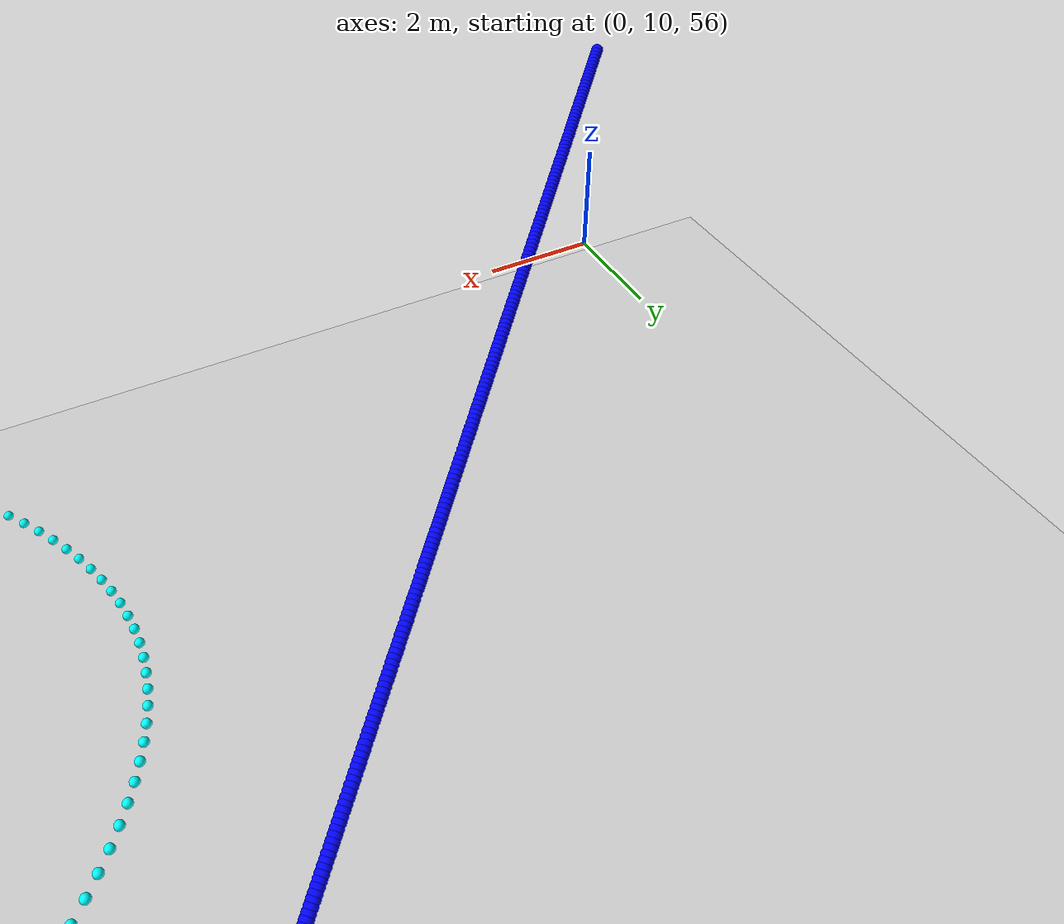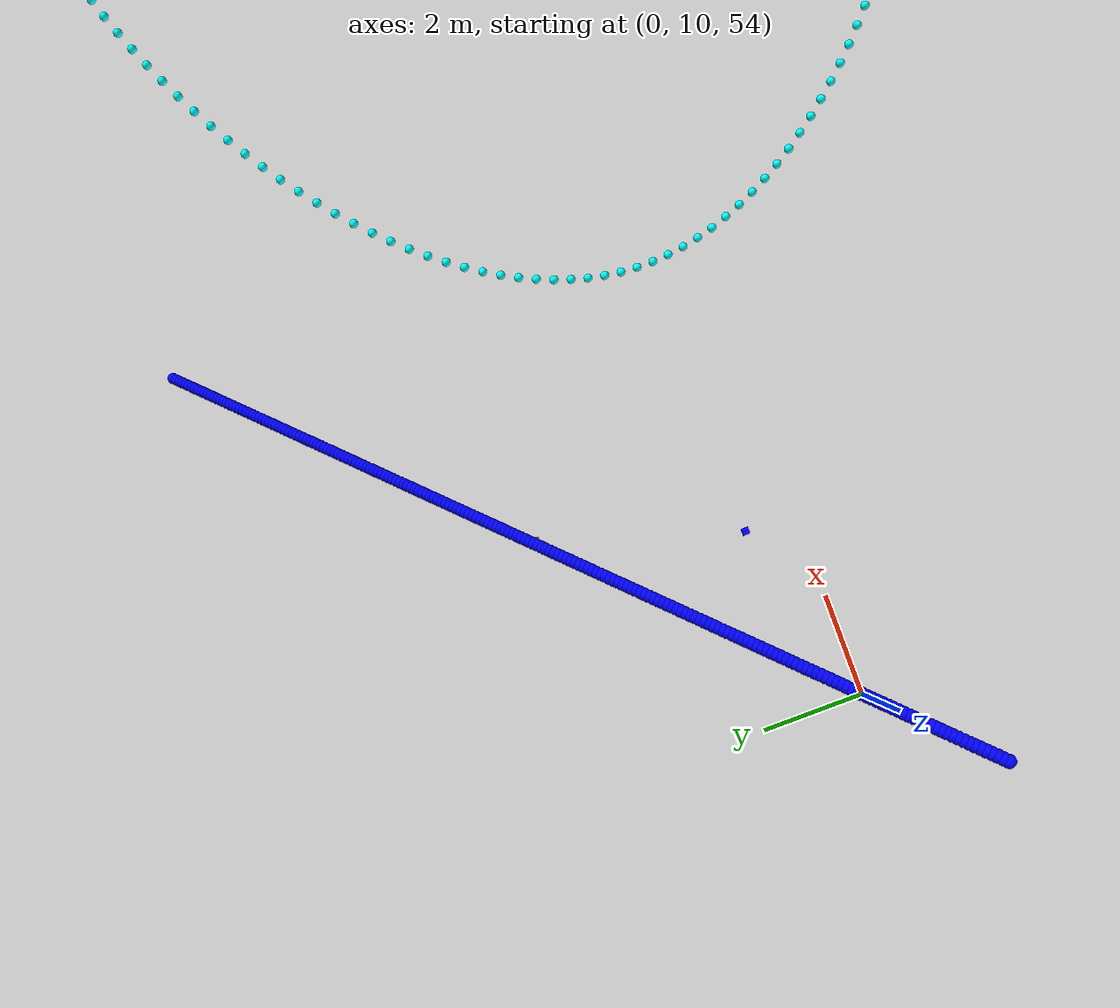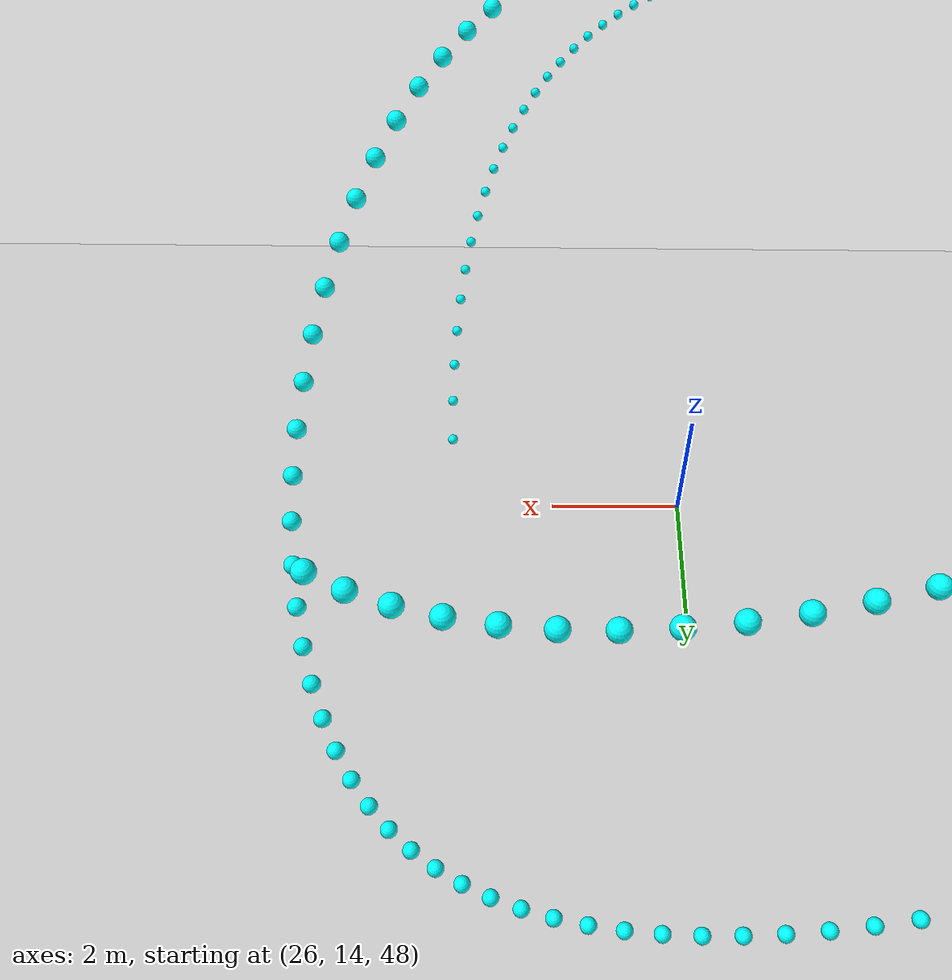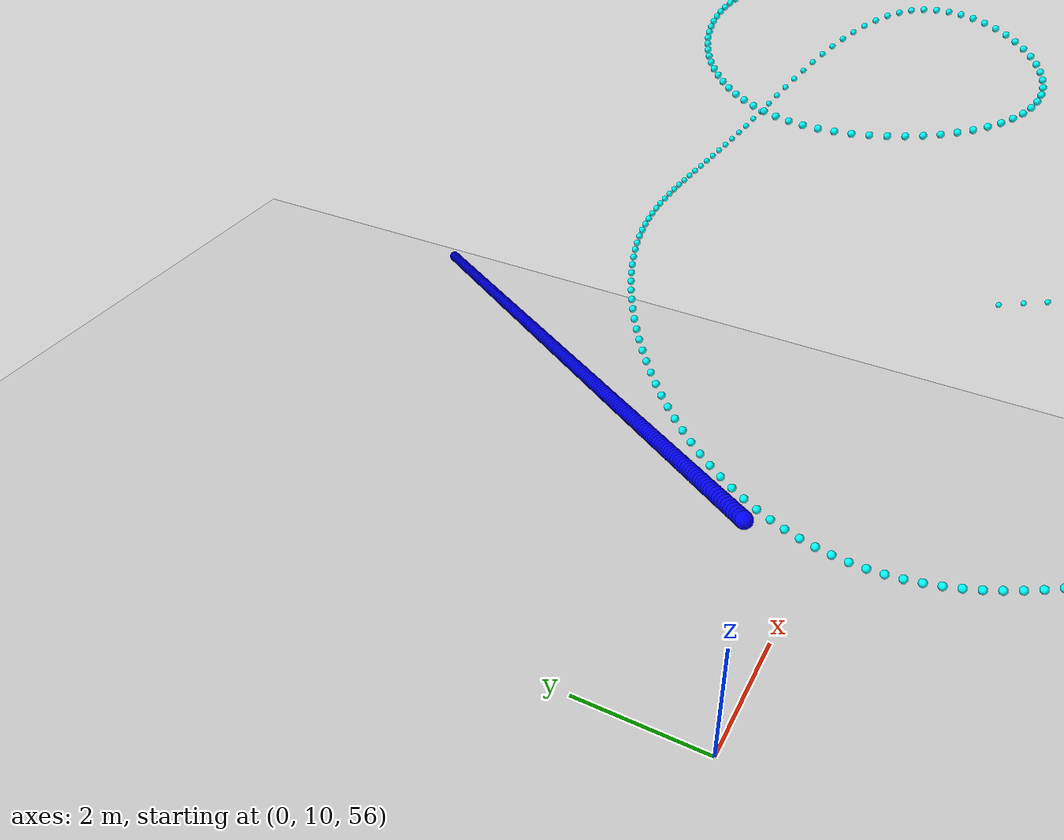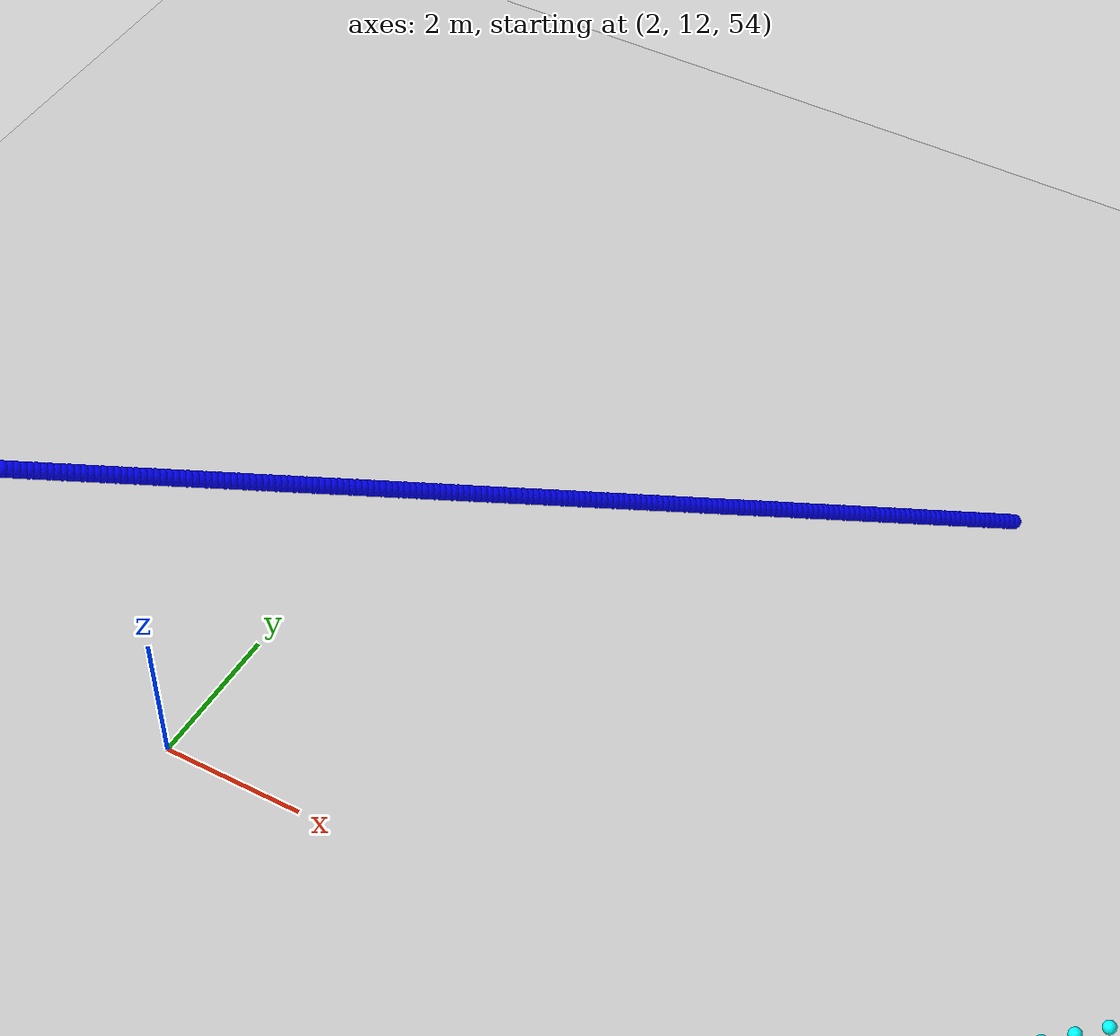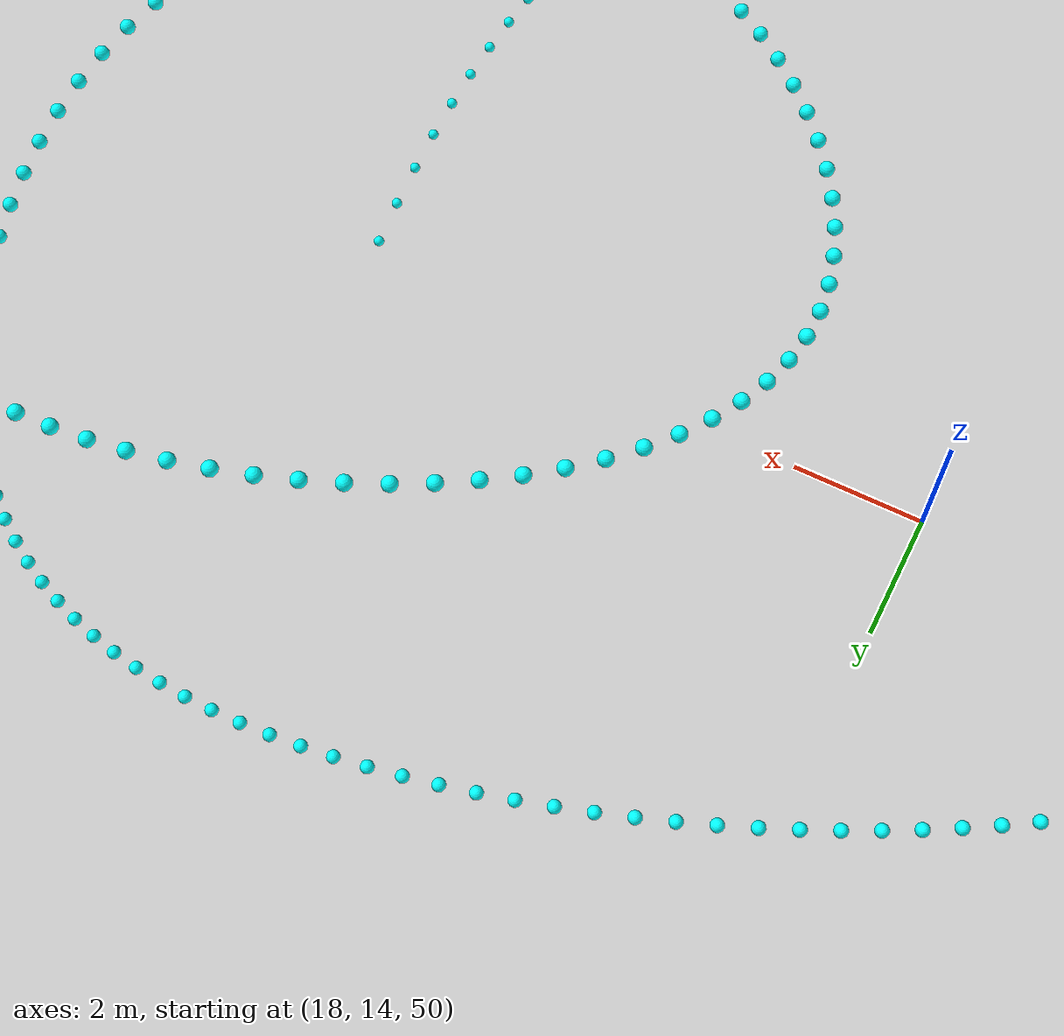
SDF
<?xml version="1.0" ?>
<sdf version="1.9">

  <world name="double_spiral_demo">

    <plugin filename="gz-sim-physics-system" name="gz::sim::systems::Physics"/>

    <plugin filename="gz-sim-user-commands-system" name="gz::sim::systems::UserCommands"/>

    <plugin filename="gz-sim-scene-broadcaster-system" name="gz::sim::systems::SceneBroadcaster"/>

    <physics name="1ms" type="ignored">

      <max_step_size>0.01</max_step_size>

      <real_time_factor>1.0</real_time_factor>

    </physics>

    <light type="directional" name="sun">

      <cast_shadows>true</cast_shadows>

      <pose>0 0 10 0 0 0</pose>

      <diffuse>0.8 0.8 0.8 1</diffuse>

      <specular>0.2 0.2 0.2 1</specular>

      <direction>-0.5 0.1 -0.9</direction>

    </light>

    <model name="ground_plane">

      <static>true</static>

      <link name="link">

        <collision name="collision">

          <geometry>
            <plane>
              <normal>0 0 1</normal>
              <size>100 100</size>
            </plane>
          </geometry>

        </collision>

        <visual name="visual">

          <geometry>
            <plane>
              <normal>0 0 1</normal>
              <size>100 100</size>
            </plane>
          </geometry>

          <material>

            <ambient>0.8 0.8 0.8 1</ambient>

            <diffuse>0.8 0.8 0.8 1</diffuse>

          </material>

        </visual>

      </link>

    </model>

    <model name="conflict_marker">

      <pose>0 0 -999 0 0 0</pose>

      <static>true</static>

      <link name="link">

        <visual name="visual">

          <geometry>
            <sphere>
              <radius>1.5</radius>
            </sphere>
          </geometry>

          <material>

            <ambient>1 0 0 1</ambient>

            <diffuse>1 0 0 1</diffuse>

            <emissive>1 0 0 1</emissive>

          </material>

        </visual>

      </link>

      <plugin name="gazebo::TrajectoryPlayer" filename="trajectory_player_plugin">

        <position_file>/tmp/gazebo_drone_positions/conflict_marker.txt</position_file>

        <update_rate>10</update_rate>

      </plugin>

    </model>

    <gui fullscreen="0">

      <camera name="user_camera">

        <pose relative_to="drone_M001">-8 -8 5 0 0.3 0.78</pose>

        <track_visual>

          <name>drone_M001</name>

          <min_dist>5</min_dist>

          <max_dist>20</max_dist>

          <static>false</static>

          <use_model_frame>true</use_model_frame>

          <xyz>-8 -8 5</xyz>

          <inherit_yaw>true</inherit_yaw>

        </track_visual>

      </camera>

    </gui>

    <model name="drone_M001">
      <pose>0 0 0 0 0 0</pose>
      <link name="body">
        <inertial>
          <mass>0.5</mass>
          <inertia>
            <ixx>0.01</ixx>
            <iyy>0.01</iyy>
            <izz>0.01</izz>
          </inertia>
        </inertial>
        <visual name="visual">
          <geometry>
            <box>
              <size>0.5 0.5 0.2</size>
            </box>
          </geometry>
          <material>
            <ambient>0 0 1 1</ambient>
            <diffuse>0 0 1 1</diffuse>
          </material>
        </visual>
      </link>
      <plugin name="gazebo::TrajectoryPlayer" filename="trajectory_player_plugin">
        <position_file>/tmp/gazebo_drone_positions/drone_M001.txt</position_file>
        <update_rate>30</update_rate>
      </plugin>
    </model>
    <model name="path_viz_M001">
      <static>true</static>
      <link name="link">
        <visual name="dot_0">
          <pose>10.0000 20.0000 55.0000 0 0 0</pose>
          <geometry>
            <sphere>
              <radius>0.10</radius>
            </sphere>
          </geometry>
          <material>
            <ambient>0 0 1 1</ambient>
            <diffuse>0 0 1 1</diffuse>
            <emissive>0 0 1 1</emissive>
          </material>
        </visual>
        <visual name="dot_1">
          <pose>9.9497 19.9497 55.0251 0 0 0</pose>
          <geometry>
            <sphere>
              <radius>0.10</radius>
            </sphere>
          </geometry>
          <material>
            <ambient>0 0 1 1</ambient>
            <diffuse>0 0 1 1</diffuse>
            <emissive>0 0 1 1</emissive>
          </material>
        </visual>
        <visual name="dot_2">
          <pose>9.8995 19.8995 55.0503 0 0 0</pose>
          <geometry>
            <sphere>
              <radius>0.10</radius>
            </sphere>
          </geometry>
          <material>
            <ambient>0 0 1 1</ambient>
            <diffuse>0 0 1 1</diffuse>
            <emissive>0 0 1 1</emissive>
          </material>
        </visual>
        <visual name="dot_3">
          <pose>9.8492 19.8492 55.0754 0 0 0</pose>
          <geometry>
            <sphere>
              <radius>0.10</radius>
            </sphere>
          </geometry>
          <material>
            <ambient>0 0 1 1</ambient>
            <diffuse>0 0 1 1</diffuse>
            <emissive>0 0 1 1</emissive>
          </material>
        </visual>
        <visual name="dot_4">
          <pose>9.7990 19.7990 55.1005 0 0 0</pose>
          <geometry>
            <sphere>
              <radius>0.10</radius>
            </sphere>
          </geometry>
          <material>
            <ambient>0 0 1 1</ambient>
            <diffuse>0 0 1 1</diffuse>
            <emissive>0 0 1 1</emissive>
          </material>
        </visual>
        <visual name="dot_5">
          <pose>9.7487 19.7487 55.1256 0 0 0</pose>
          <geometry>
            <sphere>
              <radius>0.10</radius>
            </sphere>
          </geometry>
          <material>
            <ambient>0 0 1 1</ambient>
            <diffuse>0 0 1 1</diffuse>
            <emissive>0 0 1 1</emissive>
          </material>
        </visual>
        <visual name="dot_6">
          <pose>9.6985 19.6985 55.1508 0 0 0</pose>
          <geometry>
            <sphere>
              <radius>0.10</radius>
            </sphere>
          </geometry>
          <material>
            <ambient>0 0 1 1</ambient>
            <diffuse>0 0 1 1</diffuse>
            <emissive>0 0 1 1</emissive>
          </material>
        </visual>
        <visual name="dot_7">
          <pose>9.6482 19.6482 55.1759 0 0 0</pose>
          <geometry>
            <sphere>
              <radius>0.10</radius>
            </sphere>
          </geometry>
          <material>
            <ambient>0 0 1 1</ambient>
            <diffuse>0 0 1 1</diffuse>
            <emissive>0 0 1 1</emissive>
          </material>
        </visual>
        <visual name="dot_8">
          <pose>9.5980 19.5980 55.2010 0 0 0</pose>
          <geometry>
            <sphere>
              <radius>0.10</radius>
            </sphere>
          </geometry>
          <material>
            <ambient>0 0 1 1</ambient>
            <diffuse>0 0 1 1</diffuse>
            <emissive>0 0 1 1</emissive>
          </material>
        </visual>
        <visual name="dot_9">
          <pose>9.5477 19.5477 55.2261 0 0 0</pose>
          <geometry>
            <sphere>
              <radius>0.10</radius>
            </sphere>
          </geometry>
          <material>
            <ambient>0 0 1 1</ambient>
            <diffuse>0 0 1 1</diffuse>
            <emissive>0 0 1 1</emissive>
          </material>
        </visual>
        <visual name="dot_10">
          <pose>9.4975 19.4975 55.2513 0 0 0</pose>
          <geometry>
            <sphere>
              <radius>0.10</radius>
            </sphere>
          </geometry>
          <material>
            <ambient>0 0 1 1</ambient>
            <diffuse>0 0 1 1</diffuse>
            <emissive>0 0 1 1</emissive>
          </material>
        </visual>
        <visual name="dot_11">
          <pose>9.4472 19.4472 55.2764 0 0 0</pose>
          <geometry>
            <sphere>
              <radius>0.10</radius>
            </sphere>
          </geometry>
          <material>
            <ambient>0 0 1 1</ambient>
            <diffuse>0 0 1 1</diffuse>
            <emissive>0 0 1 1</emissive>
          </material>
        </visual>
        <visual name="dot_12">
          <pose>9.3970 19.3970 55.3015 0 0 0</pose>
          <geometry>
            <sphere>
              <radius>0.10</radius>
            </sphere>
          </geometry>
          <material>
            <ambient>0 0 1 1</ambient>
            <diffuse>0 0 1 1</diffuse>
            <emissive>0 0 1 1</emissive>
          </material>
        </visual>
        <visual name="dot_13">
          <pose>9.3467 19.3467 55.3266 0 0 0</pose>
          <geometry>
            <sphere>
              <radius>0.10</radius>
            </sphere>
          </geometry>
          <material>
            <ambient>0 0 1 1</ambient>
            <diffuse>0 0 1 1</diffuse>
            <emissive>0 0 1 1</emissive>
          </material>
        </visual>
        <visual name="dot_14">
          <pose>9.2965 19.2965 55.3518 0 0 0</pose>
          <geometry>
            <sphere>
              <radius>0.10</radius>
            </sphere>
          </geometry>
          <material>
            <ambient>0 0 1 1</ambient>
            <diffuse>0 0 1 1</diffuse>
            <emissive>0 0 1 1</emissive>
          </material>
        </visual>
        <visual name="dot_15">
          <pose>9.2462 19.2462 55.3769 0 0 0</pose>
          <geometry>
            <sphere>
              <radius>0.10</radius>
            </sphere>
          </geometry>
          <material>
            <ambient>0 0 1 1</ambient>
            <diffuse>0 0 1 1</diffuse>
            <emissive>0 0 1 1</emissive>
          </material>
        </visual>
        <visual name="dot_16">
          <pose>9.1960 19.1960 55.4020 0 0 0</pose>
          <geometry>
            <sphere>
              <radius>0.10</radius>
            </sphere>
          </geometry>
          <material>
            <ambient>0 0 1 1</ambient>
            <diffuse>0 0 1 1</diffuse>
            <emissive>0 0 1 1</emissive>
          </material>
        </visual>
        <visual name="dot_17">
          <pose>9.1457 19.1457 55.4271 0 0 0</pose>
          <geometry>
            <sphere>
              <radius>0.10</radius>
            </sphere>
          </geometry>
          <material>
            <ambient>0 0 1 1</ambient>
            <diffuse>0 0 1 1</diffuse>
            <emissive>0 0 1 1</emissive>
          </material>
        </visual>
        <visual name="dot_18">
          <pose>9.0955 19.0955 55.4523 0 0 0</pose>
          <geometry>
            <sphere>
              <radius>0.10</radius>
            </sphere>
          </geometry>
          <material>
            <ambient>0 0 1 1</ambient>
            <diffuse>0 0 1 1</diffuse>
            <emissive>0 0 1 1</emissive>
          </material>
        </visual>
        <visual name="dot_19">
          <pose>9.0452 19.0452 55.4774 0 0 0</pose>
          <geometry>
            <sphere>
              <radius>0.10</radius>
            </sphere>
          </geometry>
          <material>
            <ambient>0 0 1 1</ambient>
            <diffuse>0 0 1 1</diffuse>
            <emissive>0 0 1 1</emissive>
          </material>
        </visual>
        <visual name="dot_20">
          <pose>8.9950 18.9950 55.5025 0 0 0</pose>
          <geometry>
            <sphere>
              <radius>0.10</radius>
            </sphere>
          </geometry>
          <material>
            <ambient>0 0 1 1</ambient>
            <diffuse>0 0 1 1</diffuse>
            <emissive>0 0 1 1</emissive>
          </material>
        </visual>
        <visual name="dot_21">
          <pose>8.9447 18.9447 55.5276 0 0 0</pose>
          <geometry>
            <sphere>
              <radius>0.10</radius>
            </sphere>
          </geometry>
          <material>
            <ambient>0 0 1 1</ambient>
            <diffuse>0 0 1 1</diffuse>
            <emissive>0 0 1 1</emissive>
          </material>
        </visual>
        <visual name="dot_22">
          <pose>8.8945 18.8945 55.5528 0 0 0</pose>
          <geometry>
            <sphere>
              <radius>0.10</radius>
            </sphere>
          </geometry>
          <material>
            <ambient>0 0 1 1</ambient>
            <diffuse>0 0 1 1</diffuse>
            <emissive>0 0 1 1</emissive>
          </material>
        </visual>
        <visual name="dot_23">
          <pose>8.8442 18.8442 55.5779 0 0 0</pose>
          <geometry>
            <sphere>
              <radius>0.10</radius>
            </sphere>
          </geometry>
          <material>
            <ambient>0 0 1 1</ambient>
            <diffuse>0 0 1 1</diffuse>
            <emissive>0 0 1 1</emissive>
          </material>
        </visual>
        <visual name="dot_24">
          <pose>8.7940 18.7940 55.6030 0 0 0</pose>
          <geometry>
            <sphere>
              <radius>0.10</radius>
            </sphere>
          </geometry>
          <material>
            <ambient>0 0 1 1</ambient>
            <diffuse>0 0 1 1</diffuse>
            <emissive>0 0 1 1</emissive>
          </material>
        </visual>
        <visual name="dot_25">
          <pose>8.7437 18.7437 55.6281 0 0 0</pose>
          <geometry>
            <sphere>
              <radius>0.10</radius>
            </sphere>
          </geometry>
          <material>
            <ambient>0 0 1 1</ambient>
            <diffuse>0 0 1 1</diffuse>
            <emissive>0 0 1 1</emissive>
          </material>
        </visual>
        <visual name="dot_26">
          <pose>8.6935 18.6935 55.6533 0 0 0</pose>
          <geometry>
            <sphere>
              <radius>0.10</radius>
            </sphere>
          </geometry>
          <material>
            <ambient>0 0 1 1</ambient>
            <diffuse>0 0 1 1</diffuse>
            <emissive>0 0 1 1</emissive>
          </material>
        </visual>
        <visual name="dot_27">
          <pose>8.6432 18.6432 55.6784 0 0 0</pose>
          <geometry>
            <sphere>
              <radius>0.10</radius>
            </sphere>
          </geometry>
          <material>
            <ambient>0 0 1 1</ambient>
            <diffuse>0 0 1 1</diffuse>
            <emissive>0 0 1 1</emissive>
          </material>
        </visual>
        <visual name="dot_28">
          <pose>8.5930 18.5930 55.7035 0 0 0</pose>
          <geometry>
            <sphere>
              <radius>0.10</radius>
            </sphere>
          </geometry>
          <material>
            <ambient>0 0 1 1</ambient>
            <diffuse>0 0 1 1</diffuse>
            <emissive>0 0 1 1</emissive>
          </material>
        </visual>
        <visual name="dot_29">
          <pose>8.5427 18.5427 55.7286 0 0 0</pose>
          <geometry>
            <sphere>
              <radius>0.10</radius>
            </sphere>
          </geometry>
          <material>
            <ambient>0 0 1 1</ambient>
            <diffuse>0 0 1 1</diffuse>
            <emissive>0 0 1 1</emissive>
          </material>
        </visual>
        <visual name="dot_30">
          <pose>8.4925 18.4925 55.7538 0 0 0</pose>
          <geometry>
            <sphere>
              <radius>0.10</radius>
            </sphere>
          </geometry>
          <material>
            <ambient>0 0 1 1</ambient>
            <diffuse>0 0 1 1</diffuse>
            <emissive>0 0 1 1</emissive>
          </material>
        </visual>
        <visual name="dot_31">
          <pose>8.4422 18.4422 55.7789 0 0 0</pose>
          <geometry>
            <sphere>
              <radius>0.10</radius>
            </sphere>
          </geometry>
          <material>
            <ambient>0 0 1 1</ambient>
            <diffuse>0 0 1 1</diffuse>
            <emissive>0 0 1 1</emissive>
          </material>
        </visual>
        <visual name="dot_32">
          <pose>8.3920 18.3920 55.8040 0 0 0</pose>
          <geometry>
            <sphere>
              <radius>0.10</radius>
            </sphere>
          </geometry>
          <material>
            <ambient>0 0 1 1</ambient>
            <diffuse>0 0 1 1</diffuse>
            <emissive>0 0 1 1</emissive>
          </material>
        </visual>
        <visual name="dot_33">
          <pose>8.3417 18.3417 55.8291 0 0 0</pose>
          <geometry>
            <sphere>
              <radius>0.10</radius>
            </sphere>
          </geometry>
          <material>
            <ambient>0 0 1 1</ambient>
            <diffuse>0 0 1 1</diffuse>
            <emissive>0 0 1 1</emissive>
          </material>
        </visual>
        <visual name="dot_34">
          <pose>8.2915 18.2915 55.8543 0 0 0</pose>
          <geometry>
            <sphere>
              <radius>0.10</radius>
            </sphere>
          </geometry>
          <material>
            <ambient>0 0 1 1</ambient>
            <diffuse>0 0 1 1</diffuse>
            <emissive>0 0 1 1</emissive>
          </material>
        </visual>
        <visual name="dot_35">
          <pose>8.2412 18.2412 55.8794 0 0 0</pose>
          <geometry>
            <sphere>
              <radius>0.10</radius>
            </sphere>
          </geometry>
          <material>
            <ambient>0 0 1 1</ambient>
            <diffuse>0 0 1 1</diffuse>
            <emissive>0 0 1 1</emissive>
          </material>
        </visual>
        <visual name="dot_36">
          <pose>8.1910 18.1910 55.9045 0 0 0</pose>
          <geometry>
            <sphere>
              <radius>0.10</radius>
            </sphere>
          </geometry>
          <material>
            <ambient>0 0 1 1</ambient>
            <diffuse>0 0 1 1</diffuse>
            <emissive>0 0 1 1</emissive>
          </material>
        </visual>
        <visual name="dot_37">
          <pose>8.1407 18.1407 55.9296 0 0 0</pose>
          <geometry>
            <sphere>
              <radius>0.10</radius>
            </sphere>
          </geometry>
          <material>
            <ambient>0 0 1 1</ambient>
            <diffuse>0 0 1 1</diffuse>
            <emissive>0 0 1 1</emissive>
          </material>
        </visual>
        <visual name="dot_38">
          <pose>8.0905 18.0905 55.9548 0 0 0</pose>
          <geometry>
            <sphere>
              <radius>0.10</radius>
            </sphere>
          </geometry>
          <material>
            <ambient>0 0 1 1</ambient>
            <diffuse>0 0 1 1</diffuse>
            <emissive>0 0 1 1</emissive>
          </material>
        </visual>
        <visual name="dot_39">
          <pose>8.0402 18.0402 55.9799 0 0 0</pose>
          <geometry>
            <sphere>
              <radius>0.10</radius>
            </sphere>
          </geometry>
          <material>
            <ambient>0 0 1 1</ambient>
            <diffuse>0 0 1 1</diffuse>
            <emissive>0 0 1 1</emissive>
          </material>
        </visual>
        <visual name="dot_40">
          <pose>7.9899 17.9899 56.0050 0 0 0</pose>
          <geometry>
            <sphere>
              <radius>0.10</radius>
            </sphere>
          </geometry>
          <material>
            <ambient>0 0 1 1</ambient>
            <diffuse>0 0 1 1</diffuse>
            <emissive>0 0 1 1</emissive>
          </material>
        </visual>
        <visual name="dot_41">
          <pose>7.9397 17.9397 56.0302 0 0 0</pose>
          <geometry>
            <sphere>
              <radius>0.10</radius>
            </sphere>
          </geometry>
          <material>
            <ambient>0 0 1 1</ambient>
            <diffuse>0 0 1 1</diffuse>
            <emissive>0 0 1 1</emissive>
          </material>
        </visual>
        <visual name="dot_42">
          <pose>7.8894 17.8894 56.0553 0 0 0</pose>
          <geometry>
            <sphere>
              <radius>0.10</radius>
            </sphere>
          </geometry>
          <material>
            <ambient>0 0 1 1</ambient>
            <diffuse>0 0 1 1</diffuse>
            <emissive>0 0 1 1</emissive>
          </material>
        </visual>
        <visual name="dot_43">
          <pose>7.8392 17.8392 56.0804 0 0 0</pose>
          <geometry>
            <sphere>
              <radius>0.10</radius>
            </sphere>
          </geometry>
          <material>
            <ambient>0 0 1 1</ambient>
            <diffuse>0 0 1 1</diffuse>
            <emissive>0 0 1 1</emissive>
          </material>
        </visual>
        <visual name="dot_44">
          <pose>7.7889 17.7889 56.1055 0 0 0</pose>
          <geometry>
            <sphere>
              <radius>0.10</radius>
            </sphere>
          </geometry>
          <material>
            <ambient>0 0 1 1</ambient>
            <diffuse>0 0 1 1</diffuse>
            <emissive>0 0 1 1</emissive>
          </material>
        </visual>
        <visual name="dot_45">
          <pose>7.7387 17.7387 56.1307 0 0 0</pose>
          <geometry>
            <sphere>
              <radius>0.10</radius>
            </sphere>
          </geometry>
          <material>
            <ambient>0 0 1 1</ambient>
            <diffuse>0 0 1 1</diffuse>
            <emissive>0 0 1 1</emissive>
          </material>
        </visual>
        <visual name="dot_46">
          <pose>7.6884 17.6884 56.1558 0 0 0</pose>
          <geometry>
            <sphere>
              <radius>0.10</radius>
            </sphere>
          </geometry>
          <material>
            <ambient>0 0 1 1</ambient>
            <diffuse>0 0 1 1</diffuse>
            <emissive>0 0 1 1</emissive>
          </material>
        </visual>
        <visual name="dot_47">
          <pose>7.6382 17.6382 56.1809 0 0 0</pose>
          <geometry>
            <sphere>
              <radius>0.10</radius>
            </sphere>
          </geometry>
          <material>
            <ambient>0 0 1 1</ambient>
            <diffuse>0 0 1 1</diffuse>
            <emissive>0 0 1 1</emissive>
          </material>
        </visual>
        <visual name="dot_48">
          <pose>7.5879 17.5879 56.2060 0 0 0</pose>
          <geometry>
            <sphere>
              <radius>0.10</radius>
            </sphere>
          </geometry>
          <material>
            <ambient>0 0 1 1</ambient>
            <diffuse>0 0 1 1</diffuse>
            <emissive>0 0 1 1</emissive>
          </material>
        </visual>
        <visual name="dot_49">
          <pose>7.5377 17.5377 56.2312 0 0 0</pose>
          <geometry>
            <sphere>
              <radius>0.10</radius>
            </sphere>
          </geometry>
          <material>
            <ambient>0 0 1 1</ambient>
            <diffuse>0 0 1 1</diffuse>
            <emissive>0 0 1 1</emissive>
          </material>
        </visual>
        <visual name="dot_50">
          <pose>7.4874 17.4874 56.2563 0 0 0</pose>
          <geometry>
            <sphere>
              <radius>0.10</radius>
            </sphere>
          </geometry>
          <material>
            <ambient>0 0 1 1</ambient>
            <diffuse>0 0 1 1</diffuse>
            <emissive>0 0 1 1</emissive>
          </material>
        </visual>
        <visual name="dot_51">
          <pose>7.4372 17.4372 56.2814 0 0 0</pose>
          <geometry>
            <sphere>
              <radius>0.10</radius>
            </sphere>
          </geometry>
          <material>
            <ambient>0 0 1 1</ambient>
            <diffuse>0 0 1 1</diffuse>
            <emissive>0 0 1 1</emissive>
          </material>
        </visual>
        <visual name="dot_52">
          <pose>7.3869 17.3869 56.3065 0 0 0</pose>
          <geometry>
            <sphere>
              <radius>0.10</radius>
            </sphere>
          </geometry>
          <material>
            <ambient>0 0 1 1</ambient>
            <diffuse>0 0 1 1</diffuse>
            <emissive>0 0 1 1</emissive>
          </material>
        </visual>
        <visual name="dot_53">
          <pose>7.3367 17.3367 56.3317 0 0 0</pose>
          <geometry>
            <sphere>
              <radius>0.10</radius>
            </sphere>
          </geometry>
          <material>
            <ambient>0 0 1 1</ambient>
            <diffuse>0 0 1 1</diffuse>
            <emissive>0 0 1 1</emissive>
          </material>
        </visual>
        <visual name="dot_54">
          <pose>7.2864 17.2864 56.3568 0 0 0</pose>
          <geometry>
            <sphere>
              <radius>0.10</radius>
            </sphere>
          </geometry>
          <material>
            <ambient>0 0 1 1</ambient>
            <diffuse>0 0 1 1</diffuse>
            <emissive>0 0 1 1</emissive>
          </material>
        </visual>
        <visual name="dot_55">
          <pose>7.2362 17.2362 56.3819 0 0 0</pose>
          <geometry>
            <sphere>
              <radius>0.10</radius>
            </sphere>
          </geometry>
          <material>
            <ambient>0 0 1 1</ambient>
            <diffuse>0 0 1 1</diffuse>
            <emissive>0 0 1 1</emissive>
          </material>
        </visual>
        <visual name="dot_56">
          <pose>7.1859 17.1859 56.4070 0 0 0</pose>
          <geometry>
            <sphere>
              <radius>0.10</radius>
            </sphere>
          </geometry>
          <material>
            <ambient>0 0 1 1</ambient>
            <diffuse>0 0 1 1</diffuse>
            <emissive>0 0 1 1</emissive>
          </material>
        </visual>
        <visual name="dot_57">
          <pose>7.1357 17.1357 56.4322 0 0 0</pose>
          <geometry>
            <sphere>
              <radius>0.10</radius>
            </sphere>
          </geometry>
          <material>
            <ambient>0 0 1 1</ambient>
            <diffuse>0 0 1 1</diffuse>
            <emissive>0 0 1 1</emissive>
          </material>
        </visual>
        <visual name="dot_58">
          <pose>7.0854 17.0854 56.4573 0 0 0</pose>
          <geometry>
            <sphere>
              <radius>0.10</radius>
            </sphere>
          </geometry>
          <material>
            <ambient>0 0 1 1</ambient>
            <diffuse>0 0 1 1</diffuse>
            <emissive>0 0 1 1</emissive>
          </material>
        </visual>
        <visual name="dot_59">
          <pose>7.0352 17.0352 56.4824 0 0 0</pose>
          <geometry>
            <sphere>
              <radius>0.10</radius>
            </sphere>
          </geometry>
          <material>
            <ambient>0 0 1 1</ambient>
            <diffuse>0 0 1 1</diffuse>
            <emissive>0 0 1 1</emissive>
          </material>
        </visual>
        <visual name="dot_60">
          <pose>6.9849 16.9849 56.5075 0 0 0</pose>
          <geometry>
            <sphere>
              <radius>0.10</radius>
            </sphere>
          </geometry>
          <material>
            <ambient>0 0 1 1</ambient>
            <diffuse>0 0 1 1</diffuse>
            <emissive>0 0 1 1</emissive>
          </material>
        </visual>
        <visual name="dot_61">
          <pose>6.9347 16.9347 56.5327 0 0 0</pose>
          <geometry>
            <sphere>
              <radius>0.10</radius>
            </sphere>
          </geometry>
          <material>
            <ambient>0 0 1 1</ambient>
            <diffuse>0 0 1 1</diffuse>
            <emissive>0 0 1 1</emissive>
          </material>
        </visual>
        <visual name="dot_62">
          <pose>6.8844 16.8844 56.5578 0 0 0</pose>
          <geometry>
            <sphere>
              <radius>0.10</radius>
            </sphere>
          </geometry>
          <material>
            <ambient>0 0 1 1</ambient>
            <diffuse>0 0 1 1</diffuse>
            <emissive>0 0 1 1</emissive>
          </material>
        </visual>
        <visual name="dot_63">
          <pose>6.8342 16.8342 56.5829 0 0 0</pose>
          <geometry>
            <sphere>
              <radius>0.10</radius>
            </sphere>
          </geometry>
          <material>
            <ambient>0 0 1 1</ambient>
            <diffuse>0 0 1 1</diffuse>
            <emissive>0 0 1 1</emissive>
          </material>
        </visual>
        <visual name="dot_64">
          <pose>6.7839 16.7839 56.6080 0 0 0</pose>
          <geometry>
            <sphere>
              <radius>0.10</radius>
            </sphere>
          </geometry>
          <material>
            <ambient>0 0 1 1</ambient>
            <diffuse>0 0 1 1</diffuse>
            <emissive>0 0 1 1</emissive>
          </material>
        </visual>
        <visual name="dot_65">
          <pose>6.7337 16.7337 56.6332 0 0 0</pose>
          <geometry>
            <sphere>
              <radius>0.10</radius>
            </sphere>
          </geometry>
          <material>
            <ambient>0 0 1 1</ambient>
            <diffuse>0 0 1 1</diffuse>
            <emissive>0 0 1 1</emissive>
          </material>
        </visual>
        <visual name="dot_66">
          <pose>6.6834 16.6834 56.6583 0 0 0</pose>
          <geometry>
            <sphere>
              <radius>0.10</radius>
            </sphere>
          </geometry>
          <material>
            <ambient>0 0 1 1</ambient>
            <diffuse>0 0 1 1</diffuse>
            <emissive>0 0 1 1</emissive>
          </material>
        </visual>
        <visual name="dot_67">
          <pose>6.6332 16.6332 56.6834 0 0 0</pose>
          <geometry>
            <sphere>
              <radius>0.10</radius>
            </sphere>
          </geometry>
          <material>
            <ambient>0 0 1 1</ambient>
            <diffuse>0 0 1 1</diffuse>
            <emissive>0 0 1 1</emissive>
          </material>
        </visual>
        <visual name="dot_68">
          <pose>6.5829 16.5829 56.7085 0 0 0</pose>
          <geometry>
            <sphere>
              <radius>0.10</radius>
            </sphere>
          </geometry>
          <material>
            <ambient>0 0 1 1</ambient>
            <diffuse>0 0 1 1</diffuse>
            <emissive>0 0 1 1</emissive>
          </material>
        </visual>
        <visual name="dot_69">
          <pose>6.5327 16.5327 56.7337 0 0 0</pose>
          <geometry>
            <sphere>
              <radius>0.10</radius>
            </sphere>
          </geometry>
          <material>
            <ambient>0 0 1 1</ambient>
            <diffuse>0 0 1 1</diffuse>
            <emissive>0 0 1 1</emissive>
          </material>
        </visual>
        <visual name="dot_70">
          <pose>6.4824 16.4824 56.7588 0 0 0</pose>
          <geometry>
            <sphere>
              <radius>0.10</radius>
            </sphere>
          </geometry>
          <material>
            <ambient>0 0 1 1</ambient>
            <diffuse>0 0 1 1</diffuse>
            <emissive>0 0 1 1</emissive>
          </material>
        </visual>
        <visual name="dot_71">
          <pose>6.4322 16.4322 56.7839 0 0 0</pose>
          <geometry>
            <sphere>
              <radius>0.10</radius>
            </sphere>
          </geometry>
          <material>
            <ambient>0 0 1 1</ambient>
            <diffuse>0 0 1 1</diffuse>
            <emissive>0 0 1 1</emissive>
          </material>
        </visual>
        <visual name="dot_72">
          <pose>6.3819 16.3819 56.8090 0 0 0</pose>
          <geometry>
            <sphere>
              <radius>0.10</radius>
            </sphere>
          </geometry>
          <material>
            <ambient>0 0 1 1</ambient>
            <diffuse>0 0 1 1</diffuse>
            <emissive>0 0 1 1</emissive>
          </material>
        </visual>
        <visual name="dot_73">
          <pose>6.3317 16.3317 56.8342 0 0 0</pose>
          <geometry>
            <sphere>
              <radius>0.10</radius>
            </sphere>
          </geometry>
          <material>
            <ambient>0 0 1 1</ambient>
            <diffuse>0 0 1 1</diffuse>
            <emissive>0 0 1 1</emissive>
          </material>
        </visual>
        <visual name="dot_74">
          <pose>6.2814 16.2814 56.8593 0 0 0</pose>
          <geometry>
            <sphere>
              <radius>0.10</radius>
            </sphere>
          </geometry>
          <material>
            <ambient>0 0 1 1</ambient>
            <diffuse>0 0 1 1</diffuse>
            <emissive>0 0 1 1</emissive>
          </material>
        </visual>
        <visual name="dot_75">
          <pose>6.2312 16.2312 56.8844 0 0 0</pose>
          <geometry>
            <sphere>
              <radius>0.10</radius>
            </sphere>
          </geometry>
          <material>
            <ambient>0 0 1 1</ambient>
            <diffuse>0 0 1 1</diffuse>
            <emissive>0 0 1 1</emissive>
          </material>
        </visual>
        <visual name="dot_76">
          <pose>6.1809 16.1809 56.9095 0 0 0</pose>
          <geometry>
            <sphere>
              <radius>0.10</radius>
            </sphere>
          </geometry>
          <material>
            <ambient>0 0 1 1</ambient>
            <diffuse>0 0 1 1</diffuse>
            <emissive>0 0 1 1</emissive>
          </material>
        </visual>
        <visual name="dot_77">
          <pose>6.1307 16.1307 56.9347 0 0 0</pose>
          <geometry>
            <sphere>
              <radius>0.10</radius>
            </sphere>
          </geometry>
          <material>
            <ambient>0 0 1 1</ambient>
            <diffuse>0 0 1 1</diffuse>
            <emissive>0 0 1 1</emissive>
          </material>
        </visual>
        <visual name="dot_78">
          <pose>6.0804 16.0804 56.9598 0 0 0</pose>
          <geometry>
            <sphere>
              <radius>0.10</radius>
            </sphere>
          </geometry>
          <material>
            <ambient>0 0 1 1</ambient>
            <diffuse>0 0 1 1</diffuse>
            <emissive>0 0 1 1</emissive>
          </material>
        </visual>
        <visual name="dot_79">
          <pose>6.0302 16.0302 56.9849 0 0 0</pose>
          <geometry>
            <sphere>
              <radius>0.10</radius>
            </sphere>
          </geometry>
          <material>
            <ambient>0 0 1 1</ambient>
            <diffuse>0 0 1 1</diffuse>
            <emissive>0 0 1 1</emissive>
          </material>
        </visual>
        <visual name="dot_80">
          <pose>5.9799 15.9799 57.0101 0 0 0</pose>
          <geometry>
            <sphere>
              <radius>0.10</radius>
            </sphere>
          </geometry>
          <material>
            <ambient>0 0 1 1</ambient>
            <diffuse>0 0 1 1</diffuse>
            <emissive>0 0 1 1</emissive>
          </material>
        </visual>
        <visual name="dot_81">
          <pose>5.9296 15.9296 57.0352 0 0 0</pose>
          <geometry>
            <sphere>
              <radius>0.10</radius>
            </sphere>
          </geometry>
          <material>
            <ambient>0 0 1 1</ambient>
            <diffuse>0 0 1 1</diffuse>
            <emissive>0 0 1 1</emissive>
          </material>
        </visual>
        <visual name="dot_82">
          <pose>5.8794 15.8794 57.0603 0 0 0</pose>
          <geometry>
            <sphere>
              <radius>0.10</radius>
            </sphere>
          </geometry>
          <material>
            <ambient>0 0 1 1</ambient>
            <diffuse>0 0 1 1</diffuse>
            <emissive>0 0 1 1</emissive>
          </material>
        </visual>
        <visual name="dot_83">
          <pose>5.8291 15.8291 57.0854 0 0 0</pose>
          <geometry>
            <sphere>
              <radius>0.10</radius>
            </sphere>
          </geometry>
          <material>
            <ambient>0 0 1 1</ambient>
            <diffuse>0 0 1 1</diffuse>
            <emissive>0 0 1 1</emissive>
          </material>
        </visual>
        <visual name="dot_84">
          <pose>5.7789 15.7789 57.1106 0 0 0</pose>
          <geometry>
            <sphere>
              <radius>0.10</radius>
            </sphere>
          </geometry>
          <material>
            <ambient>0 0 1 1</ambient>
            <diffuse>0 0 1 1</diffuse>
            <emissive>0 0 1 1</emissive>
          </material>
        </visual>
        <visual name="dot_85">
          <pose>5.7286 15.7286 57.1357 0 0 0</pose>
          <geometry>
            <sphere>
              <radius>0.10</radius>
            </sphere>
          </geometry>
          <material>
            <ambient>0 0 1 1</ambient>
            <diffuse>0 0 1 1</diffuse>
            <emissive>0 0 1 1</emissive>
          </material>
        </visual>
        <visual name="dot_86">
          <pose>5.6784 15.6784 57.1608 0 0 0</pose>
          <geometry>
            <sphere>
              <radius>0.10</radius>
            </sphere>
          </geometry>
          <material>
            <ambient>0 0 1 1</ambient>
            <diffuse>0 0 1 1</diffuse>
            <emissive>0 0 1 1</emissive>
          </material>
        </visual>
        <visual name="dot_87">
          <pose>5.6281 15.6281 57.1859 0 0 0</pose>
          <geometry>
            <sphere>
              <radius>0.10</radius>
            </sphere>
          </geometry>
          <material>
            <ambient>0 0 1 1</ambient>
            <diffuse>0 0 1 1</diffuse>
            <emissive>0 0 1 1</emissive>
          </material>
        </visual>
        <visual name="dot_88">
          <pose>5.5779 15.5779 57.2111 0 0 0</pose>
          <geometry>
            <sphere>
              <radius>0.10</radius>
            </sphere>
          </geometry>
          <material>
            <ambient>0 0 1 1</ambient>
            <diffuse>0 0 1 1</diffuse>
            <emissive>0 0 1 1</emissive>
          </material>
        </visual>
        <visual name="dot_89">
          <pose>5.5276 15.5276 57.2362 0 0 0</pose>
          <geometry>
            <sphere>
              <radius>0.10</radius>
            </sphere>
          </geometry>
          <material>
            <ambient>0 0 1 1</ambient>
            <diffuse>0 0 1 1</diffuse>
            <emissive>0 0 1 1</emissive>
          </material>
        </visual>
        <visual name="dot_90">
          <pose>5.4774 15.4774 57.2613 0 0 0</pose>
          <geometry>
            <sphere>
              <radius>0.10</radius>
            </sphere>
          </geometry>
          <material>
            <ambient>0 0 1 1</ambient>
            <diffuse>0 0 1 1</diffuse>
            <emissive>0 0 1 1</emissive>
          </material>
        </visual>
        <visual name="dot_91">
          <pose>5.4271 15.4271 57.2864 0 0 0</pose>
          <geometry>
            <sphere>
              <radius>0.10</radius>
            </sphere>
          </geometry>
          <material>
            <ambient>0 0 1 1</ambient>
            <diffuse>0 0 1 1</diffuse>
            <emissive>0 0 1 1</emissive>
          </material>
        </visual>
        <visual name="dot_92">
          <pose>5.3769 15.3769 57.3116 0 0 0</pose>
          <geometry>
            <sphere>
              <radius>0.10</radius>
            </sphere>
          </geometry>
          <material>
            <ambient>0 0 1 1</ambient>
            <diffuse>0 0 1 1</diffuse>
            <emissive>0 0 1 1</emissive>
          </material>
        </visual>
        <visual name="dot_93">
          <pose>5.3266 15.3266 57.3367 0 0 0</pose>
          <geometry>
            <sphere>
              <radius>0.10</radius>
            </sphere>
          </geometry>
          <material>
            <ambient>0 0 1 1</ambient>
            <diffuse>0 0 1 1</diffuse>
            <emissive>0 0 1 1</emissive>
          </material>
        </visual>
        <visual name="dot_94">
          <pose>5.2764 15.2764 57.3618 0 0 0</pose>
          <geometry>
            <sphere>
              <radius>0.10</radius>
            </sphere>
          </geometry>
          <material>
            <ambient>0 0 1 1</ambient>
            <diffuse>0 0 1 1</diffuse>
            <emissive>0 0 1 1</emissive>
          </material>
        </visual>
        <visual name="dot_95">
          <pose>5.2261 15.2261 57.3869 0 0 0</pose>
          <geometry>
            <sphere>
              <radius>0.10</radius>
            </sphere>
          </geometry>
          <material>
            <ambient>0 0 1 1</ambient>
            <diffuse>0 0 1 1</diffuse>
            <emissive>0 0 1 1</emissive>
          </material>
        </visual>
        <visual name="dot_96">
          <pose>5.1759 15.1759 57.4121 0 0 0</pose>
          <geometry>
            <sphere>
              <radius>0.10</radius>
            </sphere>
          </geometry>
          <material>
            <ambient>0 0 1 1</ambient>
            <diffuse>0 0 1 1</diffuse>
            <emissive>0 0 1 1</emissive>
          </material>
        </visual>
        <visual name="dot_97">
          <pose>5.1256 15.1256 57.4372 0 0 0</pose>
          <geometry>
            <sphere>
              <radius>0.10</radius>
            </sphere>
          </geometry>
          <material>
            <ambient>0 0 1 1</ambient>
            <diffuse>0 0 1 1</diffuse>
            <emissive>0 0 1 1</emissive>
          </material>
        </visual>
        <visual name="dot_98">
          <pose>5.0754 15.0754 57.4623 0 0 0</pose>
          <geometry>
            <sphere>
              <radius>0.10</radius>
            </sphere>
          </geometry>
          <material>
            <ambient>0 0 1 1</ambient>
            <diffuse>0 0 1 1</diffuse>
            <emissive>0 0 1 1</emissive>
          </material>
        </visual>
        <visual name="dot_99">
          <pose>5.0251 15.0251 57.4874 0 0 0</pose>
          <geometry>
            <sphere>
              <radius>0.10</radius>
            </sphere>
          </geometry>
          <material>
            <ambient>0 0 1 1</ambient>
            <diffuse>0 0 1 1</diffuse>
            <emissive>0 0 1 1</emissive>
          </material>
        </visual>
        <visual name="dot_100">
          <pose>4.9749 14.9749 57.5126 0 0 0</pose>
          <geometry>
            <sphere>
              <radius>0.10</radius>
            </sphere>
          </geometry>
          <material>
            <ambient>0 0 1 1</ambient>
            <diffuse>0 0 1 1</diffuse>
            <emissive>0 0 1 1</emissive>
          </material>
        </visual>
        <visual name="dot_101">
          <pose>4.9246 14.9246 57.5377 0 0 0</pose>
          <geometry>
            <sphere>
              <radius>0.10</radius>
            </sphere>
          </geometry>
          <material>
            <ambient>0 0 1 1</ambient>
            <diffuse>0 0 1 1</diffuse>
            <emissive>0 0 1 1</emissive>
          </material>
        </visual>
        <visual name="dot_102">
          <pose>4.8744 14.8744 57.5628 0 0 0</pose>
          <geometry>
            <sphere>
              <radius>0.10</radius>
            </sphere>
          </geometry>
          <material>
            <ambient>0 0 1 1</ambient>
            <diffuse>0 0 1 1</diffuse>
            <emissive>0 0 1 1</emissive>
          </material>
        </visual>
        <visual name="dot_103">
          <pose>4.8241 14.8241 57.5879 0 0 0</pose>
          <geometry>
            <sphere>
              <radius>0.10</radius>
            </sphere>
          </geometry>
          <material>
            <ambient>0 0 1 1</ambient>
            <diffuse>0 0 1 1</diffuse>
            <emissive>0 0 1 1</emissive>
          </material>
        </visual>
        <visual name="dot_104">
          <pose>4.7739 14.7739 57.6131 0 0 0</pose>
          <geometry>
            <sphere>
              <radius>0.10</radius>
            </sphere>
          </geometry>
          <material>
            <ambient>0 0 1 1</ambient>
            <diffuse>0 0 1 1</diffuse>
            <emissive>0 0 1 1</emissive>
          </material>
        </visual>
        <visual name="dot_105">
          <pose>4.7236 14.7236 57.6382 0 0 0</pose>
          <geometry>
            <sphere>
              <radius>0.10</radius>
            </sphere>
          </geometry>
          <material>
            <ambient>0 0 1 1</ambient>
            <diffuse>0 0 1 1</diffuse>
            <emissive>0 0 1 1</emissive>
          </material>
        </visual>
        <visual name="dot_106">
          <pose>4.6734 14.6734 57.6633 0 0 0</pose>
          <geometry>
            <sphere>
              <radius>0.10</radius>
            </sphere>
          </geometry>
          <material>
            <ambient>0 0 1 1</ambient>
            <diffuse>0 0 1 1</diffuse>
            <emissive>0 0 1 1</emissive>
          </material>
        </visual>
        <visual name="dot_107">
          <pose>4.6231 14.6231 57.6884 0 0 0</pose>
          <geometry>
            <sphere>
              <radius>0.10</radius>
            </sphere>
          </geometry>
          <material>
            <ambient>0 0 1 1</ambient>
            <diffuse>0 0 1 1</diffuse>
            <emissive>0 0 1 1</emissive>
          </material>
        </visual>
        <visual name="dot_108">
          <pose>4.5729 14.5729 57.7136 0 0 0</pose>
          <geometry>
            <sphere>
              <radius>0.10</radius>
            </sphere>
          </geometry>
          <material>
            <ambient>0 0 1 1</ambient>
            <diffuse>0 0 1 1</diffuse>
            <emissive>0 0 1 1</emissive>
          </material>
        </visual>
        <visual name="dot_109">
          <pose>4.5226 14.5226 57.7387 0 0 0</pose>
          <geometry>
            <sphere>
              <radius>0.10</radius>
            </sphere>
          </geometry>
          <material>
            <ambient>0 0 1 1</ambient>
            <diffuse>0 0 1 1</diffuse>
            <emissive>0 0 1 1</emissive>
          </material>
        </visual>
        <visual name="dot_110">
          <pose>4.4724 14.4724 57.7638 0 0 0</pose>
          <geometry>
            <sphere>
              <radius>0.10</radius>
            </sphere>
          </geometry>
          <material>
            <ambient>0 0 1 1</ambient>
            <diffuse>0 0 1 1</diffuse>
            <emissive>0 0 1 1</emissive>
          </material>
        </visual>
        <visual name="dot_111">
          <pose>4.4221 14.4221 57.7889 0 0 0</pose>
          <geometry>
            <sphere>
              <radius>0.10</radius>
            </sphere>
          </geometry>
          <material>
            <ambient>0 0 1 1</ambient>
            <diffuse>0 0 1 1</diffuse>
            <emissive>0 0 1 1</emissive>
          </material>
        </visual>
        <visual name="dot_112">
          <pose>4.3719 14.3719 57.8141 0 0 0</pose>
          <geometry>
            <sphere>
              <radius>0.10</radius>
            </sphere>
          </geometry>
          <material>
            <ambient>0 0 1 1</ambient>
            <diffuse>0 0 1 1</diffuse>
            <emissive>0 0 1 1</emissive>
          </material>
        </visual>
        <visual name="dot_113">
          <pose>4.3216 14.3216 57.8392 0 0 0</pose>
          <geometry>
            <sphere>
              <radius>0.10</radius>
            </sphere>
          </geometry>
          <material>
            <ambient>0 0 1 1</ambient>
            <diffuse>0 0 1 1</diffuse>
            <emissive>0 0 1 1</emissive>
          </material>
        </visual>
        <visual name="dot_114">
          <pose>4.2714 14.2714 57.8643 0 0 0</pose>
          <geometry>
            <sphere>
              <radius>0.10</radius>
            </sphere>
          </geometry>
          <material>
            <ambient>0 0 1 1</ambient>
            <diffuse>0 0 1 1</diffuse>
            <emissive>0 0 1 1</emissive>
          </material>
        </visual>
        <visual name="dot_115">
          <pose>4.2211 14.2211 57.8894 0 0 0</pose>
          <geometry>
            <sphere>
              <radius>0.10</radius>
            </sphere>
          </geometry>
          <material>
            <ambient>0 0 1 1</ambient>
            <diffuse>0 0 1 1</diffuse>
            <emissive>0 0 1 1</emissive>
          </material>
        </visual>
        <visual name="dot_116">
          <pose>4.1709 14.1709 57.9146 0 0 0</pose>
          <geometry>
            <sphere>
              <radius>0.10</radius>
            </sphere>
          </geometry>
          <material>
            <ambient>0 0 1 1</ambient>
            <diffuse>0 0 1 1</diffuse>
            <emissive>0 0 1 1</emissive>
          </material>
        </visual>
        <visual name="dot_117">
          <pose>4.1206 14.1206 57.9397 0 0 0</pose>
          <geometry>
            <sphere>
              <radius>0.10</radius>
            </sphere>
          </geometry>
          <material>
            <ambient>0 0 1 1</ambient>
            <diffuse>0 0 1 1</diffuse>
            <emissive>0 0 1 1</emissive>
          </material>
        </visual>
        <visual name="dot_118">
          <pose>4.0704 14.0704 57.9648 0 0 0</pose>
          <geometry>
            <sphere>
              <radius>0.10</radius>
            </sphere>
          </geometry>
          <material>
            <ambient>0 0 1 1</ambient>
            <diffuse>0 0 1 1</diffuse>
            <emissive>0 0 1 1</emissive>
          </material>
        </visual>
        <visual name="dot_119">
          <pose>4.0201 14.0201 57.9899 0 0 0</pose>
          <geometry>
            <sphere>
              <radius>0.10</radius>
            </sphere>
          </geometry>
          <material>
            <ambient>0 0 1 1</ambient>
            <diffuse>0 0 1 1</diffuse>
            <emissive>0 0 1 1</emissive>
          </material>
        </visual>
        <visual name="dot_120">
          <pose>3.9698 13.9698 58.0151 0 0 0</pose>
          <geometry>
            <sphere>
              <radius>0.10</radius>
            </sphere>
          </geometry>
          <material>
            <ambient>0 0 1 1</ambient>
            <diffuse>0 0 1 1</diffuse>
            <emissive>0 0 1 1</emissive>
          </material>
        </visual>
        <visual name="dot_121">
          <pose>3.9196 13.9196 58.0402 0 0 0</pose>
          <geometry>
            <sphere>
              <radius>0.10</radius>
            </sphere>
          </geometry>
          <material>
            <ambient>0 0 1 1</ambient>
            <diffuse>0 0 1 1</diffuse>
            <emissive>0 0 1 1</emissive>
          </material>
        </visual>
        <visual name="dot_122">
          <pose>3.8693 13.8693 58.0653 0 0 0</pose>
          <geometry>
            <sphere>
              <radius>0.10</radius>
            </sphere>
          </geometry>
          <material>
            <ambient>0 0 1 1</ambient>
            <diffuse>0 0 1 1</diffuse>
            <emissive>0 0 1 1</emissive>
          </material>
        </visual>
        <visual name="dot_123">
          <pose>3.8191 13.8191 58.0905 0 0 0</pose>
          <geometry>
            <sphere>
              <radius>0.10</radius>
            </sphere>
          </geometry>
          <material>
            <ambient>0 0 1 1</ambient>
            <diffuse>0 0 1 1</diffuse>
            <emissive>0 0 1 1</emissive>
          </material>
        </visual>
        <visual name="dot_124">
          <pose>3.7688 13.7688 58.1156 0 0 0</pose>
          <geometry>
            <sphere>
              <radius>0.10</radius>
            </sphere>
          </geometry>
          <material>
            <ambient>0 0 1 1</ambient>
            <diffuse>0 0 1 1</diffuse>
            <emissive>0 0 1 1</emissive>
          </material>
        </visual>
        <visual name="dot_125">
          <pose>3.7186 13.7186 58.1407 0 0 0</pose>
          <geometry>
            <sphere>
              <radius>0.10</radius>
            </sphere>
          </geometry>
          <material>
            <ambient>0 0 1 1</ambient>
            <diffuse>0 0 1 1</diffuse>
            <emissive>0 0 1 1</emissive>
          </material>
        </visual>
        <visual name="dot_126">
          <pose>3.6683 13.6683 58.1658 0 0 0</pose>
          <geometry>
            <sphere>
              <radius>0.10</radius>
            </sphere>
          </geometry>
          <material>
            <ambient>0 0 1 1</ambient>
            <diffuse>0 0 1 1</diffuse>
            <emissive>0 0 1 1</emissive>
          </material>
        </visual>
        <visual name="dot_127">
          <pose>3.6181 13.6181 58.1910 0 0 0</pose>
          <geometry>
            <sphere>
              <radius>0.10</radius>
            </sphere>
          </geometry>
          <material>
            <ambient>0 0 1 1</ambient>
            <diffuse>0 0 1 1</diffuse>
            <emissive>0 0 1 1</emissive>
          </material>
        </visual>
        <visual name="dot_128">
          <pose>3.5678 13.5678 58.2161 0 0 0</pose>
          <geometry>
            <sphere>
              <radius>0.10</radius>
            </sphere>
          </geometry>
          <material>
            <ambient>0 0 1 1</ambient>
            <diffuse>0 0 1 1</diffuse>
            <emissive>0 0 1 1</emissive>
          </material>
        </visual>
        <visual name="dot_129">
          <pose>3.5176 13.5176 58.2412 0 0 0</pose>
          <geometry>
            <sphere>
              <radius>0.10</radius>
            </sphere>
          </geometry>
          <material>
            <ambient>0 0 1 1</ambient>
            <diffuse>0 0 1 1</diffuse>
            <emissive>0 0 1 1</emissive>
          </material>
        </visual>
        <visual name="dot_130">
          <pose>3.4673 13.4673 58.2663 0 0 0</pose>
          <geometry>
            <sphere>
              <radius>0.10</radius>
            </sphere>
          </geometry>
          <material>
            <ambient>0 0 1 1</ambient>
            <diffuse>0 0 1 1</diffuse>
            <emissive>0 0 1 1</emissive>
          </material>
        </visual>
        <visual name="dot_131">
          <pose>3.4171 13.4171 58.2915 0 0 0</pose>
          <geometry>
            <sphere>
              <radius>0.10</radius>
            </sphere>
          </geometry>
          <material>
            <ambient>0 0 1 1</ambient>
            <diffuse>0 0 1 1</diffuse>
            <emissive>0 0 1 1</emissive>
          </material>
        </visual>
        <visual name="dot_132">
          <pose>3.3668 13.3668 58.3166 0 0 0</pose>
          <geometry>
            <sphere>
              <radius>0.10</radius>
            </sphere>
          </geometry>
          <material>
            <ambient>0 0 1 1</ambient>
            <diffuse>0 0 1 1</diffuse>
            <emissive>0 0 1 1</emissive>
          </material>
        </visual>
        <visual name="dot_133">
          <pose>3.3166 13.3166 58.3417 0 0 0</pose>
          <geometry>
            <sphere>
              <radius>0.10</radius>
            </sphere>
          </geometry>
          <material>
            <ambient>0 0 1 1</ambient>
            <diffuse>0 0 1 1</diffuse>
            <emissive>0 0 1 1</emissive>
          </material>
        </visual>
        <visual name="dot_134">
          <pose>3.2663 13.2663 58.3668 0 0 0</pose>
          <geometry>
            <sphere>
              <radius>0.10</radius>
            </sphere>
          </geometry>
          <material>
            <ambient>0 0 1 1</ambient>
            <diffuse>0 0 1 1</diffuse>
            <emissive>0 0 1 1</emissive>
          </material>
        </visual>
        <visual name="dot_135">
          <pose>3.2161 13.2161 58.3920 0 0 0</pose>
          <geometry>
            <sphere>
              <radius>0.10</radius>
            </sphere>
          </geometry>
          <material>
            <ambient>0 0 1 1</ambient>
            <diffuse>0 0 1 1</diffuse>
            <emissive>0 0 1 1</emissive>
          </material>
        </visual>
        <visual name="dot_136">
          <pose>3.1658 13.1658 58.4171 0 0 0</pose>
          <geometry>
            <sphere>
              <radius>0.10</radius>
            </sphere>
          </geometry>
          <material>
            <ambient>0 0 1 1</ambient>
            <diffuse>0 0 1 1</diffuse>
            <emissive>0 0 1 1</emissive>
          </material>
        </visual>
        <visual name="dot_137">
          <pose>3.1156 13.1156 58.4422 0 0 0</pose>
          <geometry>
            <sphere>
              <radius>0.10</radius>
            </sphere>
          </geometry>
          <material>
            <ambient>0 0 1 1</ambient>
            <diffuse>0 0 1 1</diffuse>
            <emissive>0 0 1 1</emissive>
          </material>
        </visual>
        <visual name="dot_138">
          <pose>3.0653 13.0653 58.4673 0 0 0</pose>
          <geometry>
            <sphere>
              <radius>0.10</radius>
            </sphere>
          </geometry>
          <material>
            <ambient>0 0 1 1</ambient>
            <diffuse>0 0 1 1</diffuse>
            <emissive>0 0 1 1</emissive>
          </material>
        </visual>
        <visual name="dot_139">
          <pose>3.0151 13.0151 58.4925 0 0 0</pose>
          <geometry>
            <sphere>
              <radius>0.10</radius>
            </sphere>
          </geometry>
          <material>
            <ambient>0 0 1 1</ambient>
            <diffuse>0 0 1 1</diffuse>
            <emissive>0 0 1 1</emissive>
          </material>
        </visual>
        <visual name="dot_140">
          <pose>2.9648 12.9648 58.5176 0 0 0</pose>
          <geometry>
            <sphere>
              <radius>0.10</radius>
            </sphere>
          </geometry>
          <material>
            <ambient>0 0 1 1</ambient>
            <diffuse>0 0 1 1</diffuse>
            <emissive>0 0 1 1</emissive>
          </material>
        </visual>
        <visual name="dot_141">
          <pose>2.9146 12.9146 58.5427 0 0 0</pose>
          <geometry>
            <sphere>
              <radius>0.10</radius>
            </sphere>
          </geometry>
          <material>
            <ambient>0 0 1 1</ambient>
            <diffuse>0 0 1 1</diffuse>
            <emissive>0 0 1 1</emissive>
          </material>
        </visual>
        <visual name="dot_142">
          <pose>2.8643 12.8643 58.5678 0 0 0</pose>
          <geometry>
            <sphere>
              <radius>0.10</radius>
            </sphere>
          </geometry>
          <material>
            <ambient>0 0 1 1</ambient>
            <diffuse>0 0 1 1</diffuse>
            <emissive>0 0 1 1</emissive>
          </material>
        </visual>
        <visual name="dot_143">
          <pose>2.8141 12.8141 58.5930 0 0 0</pose>
          <geometry>
            <sphere>
              <radius>0.10</radius>
            </sphere>
          </geometry>
          <material>
            <ambient>0 0 1 1</ambient>
            <diffuse>0 0 1 1</diffuse>
            <emissive>0 0 1 1</emissive>
          </material>
        </visual>
        <visual name="dot_144">
          <pose>2.7638 12.7638 58.6181 0 0 0</pose>
          <geometry>
            <sphere>
              <radius>0.10</radius>
            </sphere>
          </geometry>
          <material>
            <ambient>0 0 1 1</ambient>
            <diffuse>0 0 1 1</diffuse>
            <emissive>0 0 1 1</emissive>
          </material>
        </visual>
        <visual name="dot_145">
          <pose>2.7136 12.7136 58.6432 0 0 0</pose>
          <geometry>
            <sphere>
              <radius>0.10</radius>
            </sphere>
          </geometry>
          <material>
            <ambient>0 0 1 1</ambient>
            <diffuse>0 0 1 1</diffuse>
            <emissive>0 0 1 1</emissive>
          </material>
        </visual>
        <visual name="dot_146">
          <pose>2.6633 12.6633 58.6683 0 0 0</pose>
          <geometry>
            <sphere>
              <radius>0.10</radius>
            </sphere>
          </geometry>
          <material>
            <ambient>0 0 1 1</ambient>
            <diffuse>0 0 1 1</diffuse>
            <emissive>0 0 1 1</emissive>
          </material>
        </visual>
        <visual name="dot_147">
          <pose>2.6131 12.6131 58.6935 0 0 0</pose>
          <geometry>
            <sphere>
              <radius>0.10</radius>
            </sphere>
          </geometry>
          <material>
            <ambient>0 0 1 1</ambient>
            <diffuse>0 0 1 1</diffuse>
            <emissive>0 0 1 1</emissive>
          </material>
        </visual>
        <visual name="dot_148">
          <pose>2.5628 12.5628 58.7186 0 0 0</pose>
          <geometry>
            <sphere>
              <radius>0.10</radius>
            </sphere>
          </geometry>
          <material>
            <ambient>0 0 1 1</ambient>
            <diffuse>0 0 1 1</diffuse>
            <emissive>0 0 1 1</emissive>
          </material>
        </visual>
        <visual name="dot_149">
          <pose>2.5126 12.5126 58.7437 0 0 0</pose>
          <geometry>
            <sphere>
              <radius>0.10</radius>
            </sphere>
          </geometry>
          <material>
            <ambient>0 0 1 1</ambient>
            <diffuse>0 0 1 1</diffuse>
            <emissive>0 0 1 1</emissive>
          </material>
        </visual>
        <visual name="dot_150">
          <pose>2.4623 12.4623 58.7688 0 0 0</pose>
          <geometry>
            <sphere>
              <radius>0.10</radius>
            </sphere>
          </geometry>
          <material>
            <ambient>0 0 1 1</ambient>
            <diffuse>0 0 1 1</diffuse>
            <emissive>0 0 1 1</emissive>
          </material>
        </visual>
        <visual name="dot_151">
          <pose>2.4121 12.4121 58.7940 0 0 0</pose>
          <geometry>
            <sphere>
              <radius>0.10</radius>
            </sphere>
          </geometry>
          <material>
            <ambient>0 0 1 1</ambient>
            <diffuse>0 0 1 1</diffuse>
            <emissive>0 0 1 1</emissive>
          </material>
        </visual>
        <visual name="dot_152">
          <pose>2.3618 12.3618 58.8191 0 0 0</pose>
          <geometry>
            <sphere>
              <radius>0.10</radius>
            </sphere>
          </geometry>
          <material>
            <ambient>0 0 1 1</ambient>
            <diffuse>0 0 1 1</diffuse>
            <emissive>0 0 1 1</emissive>
          </material>
        </visual>
        <visual name="dot_153">
          <pose>2.3116 12.3116 58.8442 0 0 0</pose>
          <geometry>
            <sphere>
              <radius>0.10</radius>
            </sphere>
          </geometry>
          <material>
            <ambient>0 0 1 1</ambient>
            <diffuse>0 0 1 1</diffuse>
            <emissive>0 0 1 1</emissive>
          </material>
        </visual>
        <visual name="dot_154">
          <pose>2.2613 12.2613 58.8693 0 0 0</pose>
          <geometry>
            <sphere>
              <radius>0.10</radius>
            </sphere>
          </geometry>
          <material>
            <ambient>0 0 1 1</ambient>
            <diffuse>0 0 1 1</diffuse>
            <emissive>0 0 1 1</emissive>
          </material>
        </visual>
        <visual name="dot_155">
          <pose>2.2111 12.2111 58.8945 0 0 0</pose>
          <geometry>
            <sphere>
              <radius>0.10</radius>
            </sphere>
          </geometry>
          <material>
            <ambient>0 0 1 1</ambient>
            <diffuse>0 0 1 1</diffuse>
            <emissive>0 0 1 1</emissive>
          </material>
        </visual>
        <visual name="dot_156">
          <pose>2.1608 12.1608 58.9196 0 0 0</pose>
          <geometry>
            <sphere>
              <radius>0.10</radius>
            </sphere>
          </geometry>
          <material>
            <ambient>0 0 1 1</ambient>
            <diffuse>0 0 1 1</diffuse>
            <emissive>0 0 1 1</emissive>
          </material>
        </visual>
        <visual name="dot_157">
          <pose>2.1106 12.1106 58.9447 0 0 0</pose>
          <geometry>
            <sphere>
              <radius>0.10</radius>
            </sphere>
          </geometry>
          <material>
            <ambient>0 0 1 1</ambient>
            <diffuse>0 0 1 1</diffuse>
            <emissive>0 0 1 1</emissive>
          </material>
        </visual>
        <visual name="dot_158">
          <pose>2.0603 12.0603 58.9698 0 0 0</pose>
          <geometry>
            <sphere>
              <radius>0.10</radius>
            </sphere>
          </geometry>
          <material>
            <ambient>0 0 1 1</ambient>
            <diffuse>0 0 1 1</diffuse>
            <emissive>0 0 1 1</emissive>
          </material>
        </visual>
        <visual name="dot_159">
          <pose>2.0101 12.0101 58.9950 0 0 0</pose>
          <geometry>
            <sphere>
              <radius>0.10</radius>
            </sphere>
          </geometry>
          <material>
            <ambient>0 0 1 1</ambient>
            <diffuse>0 0 1 1</diffuse>
            <emissive>0 0 1 1</emissive>
          </material>
        </visual>
        <visual name="dot_160">
          <pose>1.9598 11.9598 59.0201 0 0 0</pose>
          <geometry>
            <sphere>
              <radius>0.10</radius>
            </sphere>
          </geometry>
          <material>
            <ambient>0 0 1 1</ambient>
            <diffuse>0 0 1 1</diffuse>
            <emissive>0 0 1 1</emissive>
          </material>
        </visual>
        <visual name="dot_161">
          <pose>1.9095 11.9095 59.0452 0 0 0</pose>
          <geometry>
            <sphere>
              <radius>0.10</radius>
            </sphere>
          </geometry>
          <material>
            <ambient>0 0 1 1</ambient>
            <diffuse>0 0 1 1</diffuse>
            <emissive>0 0 1 1</emissive>
          </material>
        </visual>
        <visual name="dot_162">
          <pose>1.8593 11.8593 59.0704 0 0 0</pose>
          <geometry>
            <sphere>
              <radius>0.10</radius>
            </sphere>
          </geometry>
          <material>
            <ambient>0 0 1 1</ambient>
            <diffuse>0 0 1 1</diffuse>
            <emissive>0 0 1 1</emissive>
          </material>
        </visual>
        <visual name="dot_163">
          <pose>1.8090 11.8090 59.0955 0 0 0</pose>
          <geometry>
            <sphere>
              <radius>0.10</radius>
            </sphere>
          </geometry>
          <material>
            <ambient>0 0 1 1</ambient>
            <diffuse>0 0 1 1</diffuse>
            <emissive>0 0 1 1</emissive>
          </material>
        </visual>
        <visual name="dot_164">
          <pose>1.7588 11.7588 59.1206 0 0 0</pose>
          <geometry>
            <sphere>
              <radius>0.10</radius>
            </sphere>
          </geometry>
          <material>
            <ambient>0 0 1 1</ambient>
            <diffuse>0 0 1 1</diffuse>
            <emissive>0 0 1 1</emissive>
          </material>
        </visual>
        <visual name="dot_165">
          <pose>1.7085 11.7085 59.1457 0 0 0</pose>
          <geometry>
            <sphere>
              <radius>0.10</radius>
            </sphere>
          </geometry>
          <material>
            <ambient>0 0 1 1</ambient>
            <diffuse>0 0 1 1</diffuse>
            <emissive>0 0 1 1</emissive>
          </material>
        </visual>
        <visual name="dot_166">
          <pose>1.6583 11.6583 59.1709 0 0 0</pose>
          <geometry>
            <sphere>
              <radius>0.10</radius>
            </sphere>
          </geometry>
          <material>
            <ambient>0 0 1 1</ambient>
            <diffuse>0 0 1 1</diffuse>
            <emissive>0 0 1 1</emissive>
          </material>
        </visual>
        <visual name="dot_167">
          <pose>1.6080 11.6080 59.1960 0 0 0</pose>
          <geometry>
            <sphere>
              <radius>0.10</radius>
            </sphere>
          </geometry>
          <material>
            <ambient>0 0 1 1</ambient>
            <diffuse>0 0 1 1</diffuse>
            <emissive>0 0 1 1</emissive>
          </material>
        </visual>
        <visual name="dot_168">
          <pose>1.5578 11.5578 59.2211 0 0 0</pose>
          <geometry>
            <sphere>
              <radius>0.10</radius>
            </sphere>
          </geometry>
          <material>
            <ambient>0 0 1 1</ambient>
            <diffuse>0 0 1 1</diffuse>
            <emissive>0 0 1 1</emissive>
          </material>
        </visual>
        <visual name="dot_169">
          <pose>1.5075 11.5075 59.2462 0 0 0</pose>
          <geometry>
            <sphere>
              <radius>0.10</radius>
            </sphere>
          </geometry>
          <material>
            <ambient>0 0 1 1</ambient>
            <diffuse>0 0 1 1</diffuse>
            <emissive>0 0 1 1</emissive>
          </material>
        </visual>
        <visual name="dot_170">
          <pose>1.4573 11.4573 59.2714 0 0 0</pose>
          <geometry>
            <sphere>
              <radius>0.10</radius>
            </sphere>
          </geometry>
          <material>
            <ambient>0 0 1 1</ambient>
            <diffuse>0 0 1 1</diffuse>
            <emissive>0 0 1 1</emissive>
          </material>
        </visual>
        <visual name="dot_171">
          <pose>1.4070 11.4070 59.2965 0 0 0</pose>
          <geometry>
            <sphere>
              <radius>0.10</radius>
            </sphere>
          </geometry>
          <material>
            <ambient>0 0 1 1</ambient>
            <diffuse>0 0 1 1</diffuse>
            <emissive>0 0 1 1</emissive>
          </material>
        </visual>
        <visual name="dot_172">
          <pose>1.3568 11.3568 59.3216 0 0 0</pose>
          <geometry>
            <sphere>
              <radius>0.10</radius>
            </sphere>
          </geometry>
          <material>
            <ambient>0 0 1 1</ambient>
            <diffuse>0 0 1 1</diffuse>
            <emissive>0 0 1 1</emissive>
          </material>
        </visual>
        <visual name="dot_173">
          <pose>1.3065 11.3065 59.3467 0 0 0</pose>
          <geometry>
            <sphere>
              <radius>0.10</radius>
            </sphere>
          </geometry>
          <material>
            <ambient>0 0 1 1</ambient>
            <diffuse>0 0 1 1</diffuse>
            <emissive>0 0 1 1</emissive>
          </material>
        </visual>
        <visual name="dot_174">
          <pose>1.2563 11.2563 59.3719 0 0 0</pose>
          <geometry>
            <sphere>
              <radius>0.10</radius>
            </sphere>
          </geometry>
          <material>
            <ambient>0 0 1 1</ambient>
            <diffuse>0 0 1 1</diffuse>
            <emissive>0 0 1 1</emissive>
          </material>
        </visual>
        <visual name="dot_175">
          <pose>1.2060 11.2060 59.3970 0 0 0</pose>
          <geometry>
            <sphere>
              <radius>0.10</radius>
            </sphere>
          </geometry>
          <material>
            <ambient>0 0 1 1</ambient>
            <diffuse>0 0 1 1</diffuse>
            <emissive>0 0 1 1</emissive>
          </material>
        </visual>
        <visual name="dot_176">
          <pose>1.1558 11.1558 59.4221 0 0 0</pose>
          <geometry>
            <sphere>
              <radius>0.10</radius>
            </sphere>
          </geometry>
          <material>
            <ambient>0 0 1 1</ambient>
            <diffuse>0 0 1 1</diffuse>
            <emissive>0 0 1 1</emissive>
          </material>
        </visual>
        <visual name="dot_177">
          <pose>1.1055 11.1055 59.4472 0 0 0</pose>
          <geometry>
            <sphere>
              <radius>0.10</radius>
            </sphere>
          </geometry>
          <material>
            <ambient>0 0 1 1</ambient>
            <diffuse>0 0 1 1</diffuse>
            <emissive>0 0 1 1</emissive>
          </material>
        </visual>
        <visual name="dot_178">
          <pose>1.0553 11.0553 59.4724 0 0 0</pose>
          <geometry>
            <sphere>
              <radius>0.10</radius>
            </sphere>
          </geometry>
          <material>
            <ambient>0 0 1 1</ambient>
            <diffuse>0 0 1 1</diffuse>
            <emissive>0 0 1 1</emissive>
          </material>
        </visual>
        <visual name="dot_179">
          <pose>1.0050 11.0050 59.4975 0 0 0</pose>
          <geometry>
            <sphere>
              <radius>0.10</radius>
            </sphere>
          </geometry>
          <material>
            <ambient>0 0 1 1</ambient>
            <diffuse>0 0 1 1</diffuse>
            <emissive>0 0 1 1</emissive>
          </material>
        </visual>
        <visual name="dot_180">
          <pose>0.9548 10.9548 59.5226 0 0 0</pose>
          <geometry>
            <sphere>
              <radius>0.10</radius>
            </sphere>
          </geometry>
          <material>
            <ambient>0 0 1 1</ambient>
            <diffuse>0 0 1 1</diffuse>
            <emissive>0 0 1 1</emissive>
          </material>
        </visual>
        <visual name="dot_181">
          <pose>0.9045 10.9045 59.5477 0 0 0</pose>
          <geometry>
            <sphere>
              <radius>0.10</radius>
            </sphere>
          </geometry>
          <material>
            <ambient>0 0 1 1</ambient>
            <diffuse>0 0 1 1</diffuse>
            <emissive>0 0 1 1</emissive>
          </material>
        </visual>
        <visual name="dot_182">
          <pose>0.8543 10.8543 59.5729 0 0 0</pose>
          <geometry>
            <sphere>
              <radius>0.10</radius>
            </sphere>
          </geometry>
          <material>
            <ambient>0 0 1 1</ambient>
            <diffuse>0 0 1 1</diffuse>
            <emissive>0 0 1 1</emissive>
          </material>
        </visual>
        <visual name="dot_183">
          <pose>0.8040 10.8040 59.5980 0 0 0</pose>
          <geometry>
            <sphere>
              <radius>0.10</radius>
            </sphere>
          </geometry>
          <material>
            <ambient>0 0 1 1</ambient>
            <diffuse>0 0 1 1</diffuse>
            <emissive>0 0 1 1</emissive>
          </material>
        </visual>
        <visual name="dot_184">
          <pose>0.7538 10.7538 59.6231 0 0 0</pose>
          <geometry>
            <sphere>
              <radius>0.10</radius>
            </sphere>
          </geometry>
          <material>
            <ambient>0 0 1 1</ambient>
            <diffuse>0 0 1 1</diffuse>
            <emissive>0 0 1 1</emissive>
          </material>
        </visual>
        <visual name="dot_185">
          <pose>0.7035 10.7035 59.6482 0 0 0</pose>
          <geometry>
            <sphere>
              <radius>0.10</radius>
            </sphere>
          </geometry>
          <material>
            <ambient>0 0 1 1</ambient>
            <diffuse>0 0 1 1</diffuse>
            <emissive>0 0 1 1</emissive>
          </material>
        </visual>
        <visual name="dot_186">
          <pose>0.6533 10.6533 59.6734 0 0 0</pose>
          <geometry>
            <sphere>
              <radius>0.10</radius>
            </sphere>
          </geometry>
          <material>
            <ambient>0 0 1 1</ambient>
            <diffuse>0 0 1 1</diffuse>
            <emissive>0 0 1 1</emissive>
          </material>
        </visual>
        <visual name="dot_187">
          <pose>0.6030 10.6030 59.6985 0 0 0</pose>
          <geometry>
            <sphere>
              <radius>0.10</radius>
            </sphere>
          </geometry>
          <material>
            <ambient>0 0 1 1</ambient>
            <diffuse>0 0 1 1</diffuse>
            <emissive>0 0 1 1</emissive>
          </material>
        </visual>
        <visual name="dot_188">
          <pose>0.5528 10.5528 59.7236 0 0 0</pose>
          <geometry>
            <sphere>
              <radius>0.10</radius>
            </sphere>
          </geometry>
          <material>
            <ambient>0 0 1 1</ambient>
            <diffuse>0 0 1 1</diffuse>
            <emissive>0 0 1 1</emissive>
          </material>
        </visual>
        <visual name="dot_189">
          <pose>0.5025 10.5025 59.7487 0 0 0</pose>
          <geometry>
            <sphere>
              <radius>0.10</radius>
            </sphere>
          </geometry>
          <material>
            <ambient>0 0 1 1</ambient>
            <diffuse>0 0 1 1</diffuse>
            <emissive>0 0 1 1</emissive>
          </material>
        </visual>
        <visual name="dot_190">
          <pose>0.4523 10.4523 59.7739 0 0 0</pose>
          <geometry>
            <sphere>
              <radius>0.10</radius>
            </sphere>
          </geometry>
          <material>
            <ambient>0 0 1 1</ambient>
            <diffuse>0 0 1 1</diffuse>
            <emissive>0 0 1 1</emissive>
          </material>
        </visual>
        <visual name="dot_191">
          <pose>0.4020 10.4020 59.7990 0 0 0</pose>
          <geometry>
            <sphere>
              <radius>0.10</radius>
            </sphere>
          </geometry>
          <material>
            <ambient>0 0 1 1</ambient>
            <diffuse>0 0 1 1</diffuse>
            <emissive>0 0 1 1</emissive>
          </material>
        </visual>
        <visual name="dot_192">
          <pose>0.3518 10.3518 59.8241 0 0 0</pose>
          <geometry>
            <sphere>
              <radius>0.10</radius>
            </sphere>
          </geometry>
          <material>
            <ambient>0 0 1 1</ambient>
            <diffuse>0 0 1 1</diffuse>
            <emissive>0 0 1 1</emissive>
          </material>
        </visual>
        <visual name="dot_193">
          <pose>0.3015 10.3015 59.8492 0 0 0</pose>
          <geometry>
            <sphere>
              <radius>0.10</radius>
            </sphere>
          </geometry>
          <material>
            <ambient>0 0 1 1</ambient>
            <diffuse>0 0 1 1</diffuse>
            <emissive>0 0 1 1</emissive>
          </material>
        </visual>
        <visual name="dot_194">
          <pose>0.2513 10.2513 59.8744 0 0 0</pose>
          <geometry>
            <sphere>
              <radius>0.10</radius>
            </sphere>
          </geometry>
          <material>
            <ambient>0 0 1 1</ambient>
            <diffuse>0 0 1 1</diffuse>
            <emissive>0 0 1 1</emissive>
          </material>
        </visual>
        <visual name="dot_195">
          <pose>0.2010 10.2010 59.8995 0 0 0</pose>
          <geometry>
            <sphere>
              <radius>0.10</radius>
            </sphere>
          </geometry>
          <material>
            <ambient>0 0 1 1</ambient>
            <diffuse>0 0 1 1</diffuse>
            <emissive>0 0 1 1</emissive>
          </material>
        </visual>
        <visual name="dot_196">
          <pose>0.1508 10.1508 59.9246 0 0 0</pose>
          <geometry>
            <sphere>
              <radius>0.10</radius>
            </sphere>
          </geometry>
          <material>
            <ambient>0 0 1 1</ambient>
            <diffuse>0 0 1 1</diffuse>
            <emissive>0 0 1 1</emissive>
          </material>
        </visual>
        <visual name="dot_197">
          <pose>0.1005 10.1005 59.9497 0 0 0</pose>
          <geometry>
            <sphere>
              <radius>0.10</radius>
            </sphere>
          </geometry>
          <material>
            <ambient>0 0 1 1</ambient>
            <diffuse>0 0 1 1</diffuse>
            <emissive>0 0 1 1</emissive>
          </material>
        </visual>
        <visual name="dot_198">
          <pose>0.0503 10.0503 59.9749 0 0 0</pose>
          <geometry>
            <sphere>
              <radius>0.10</radius>
            </sphere>
          </geometry>
          <material>
            <ambient>0 0 1 1</ambient>
            <diffuse>0 0 1 1</diffuse>
            <emissive>0 0 1 1</emissive>
          </material>
        </visual>
        <visual name="dot_199">
          <pose>0.0000 10.0000 60.0000 0 0 0</pose>
          <geometry>
            <sphere>
              <radius>0.10</radius>
            </sphere>
          </geometry>
          <material>
            <ambient>0 0 1 1</ambient>
            <diffuse>0 0 1 1</diffuse>
            <emissive>0 0 1 1</emissive>
          </material>
        </visual>
      </link>
    </model>
    <model name="drone_M002">
      <pose>0 0 0 0 0 0</pose>
      <link name="body">
        <inertial>
          <mass>0.5</mass>
          <inertia>
            <ixx>0.01</ixx>
            <iyy>0.01</iyy>
            <izz>0.01</izz>
          </inertia>
        </inertial>
        <visual name="visual">
          <geometry>
            <box>
              <size>0.5 0.5 0.2</size>
            </box>
          </geometry>
          <material>
            <ambient>0 1 1 1</ambient>
            <diffuse>0 1 1 1</diffuse>
          </material>
        </visual>
      </link>
      <plugin name="gazebo::TrajectoryPlayer" filename="trajectory_player_plugin">
        <position_file>/tmp/gazebo_drone_positions/drone_M002.txt</position_file>
        <update_rate>30</update_rate>
      </plugin>
    </model>
    <model name="path_viz_M002">
      <static>true</static>
      <link name="link">
        <visual name="dot_0">
          <pose>30.0000 20.0000 55.0000 0 0 0</pose>
          <geometry>
            <sphere>
              <radius>0.10</radius>
            </sphere>
          </geometry>
          <material>
            <ambient>0 1 1 1</ambient>
            <diffuse>0 1 1 1</diffuse>
            <emissive>0 1 1 1</emissive>
          </material>
        </visual>
        <visual name="dot_1">
          <pose>29.6735 20.1564 54.9913 0 0 0</pose>
          <geometry>
            <sphere>
              <radius>0.10</radius>
            </sphere>
          </geometry>
          <material>
            <ambient>0 1 1 1</ambient>
            <diffuse>0 1 1 1</diffuse>
            <emissive>0 1 1 1</emissive>
          </material>
        </visual>
        <visual name="dot_2">
          <pose>29.3157 20.2803 54.9849 0 0 0</pose>
          <geometry>
            <sphere>
              <radius>0.10</radius>
            </sphere>
          </geometry>
          <material>
            <ambient>0 1 1 1</ambient>
            <diffuse>0 1 1 1</diffuse>
            <emissive>0 1 1 1</emissive>
          </material>
        </visual>
        <visual name="dot_3">
          <pose>28.9300 20.3725 54.9806 0 0 0</pose>
          <geometry>
            <sphere>
              <radius>0.10</radius>
            </sphere>
          </geometry>
          <material>
            <ambient>0 1 1 1</ambient>
            <diffuse>0 1 1 1</diffuse>
            <emissive>0 1 1 1</emissive>
          </material>
        </visual>
        <visual name="dot_4">
          <pose>28.5197 20.4339 54.9780 0 0 0</pose>
          <geometry>
            <sphere>
              <radius>0.10</radius>
            </sphere>
          </geometry>
          <material>
            <ambient>0 1 1 1</ambient>
            <diffuse>0 1 1 1</diffuse>
            <emissive>0 1 1 1</emissive>
          </material>
        </visual>
        <visual name="dot_5">
          <pose>28.0882 20.4654 54.9772 0 0 0</pose>
          <geometry>
            <sphere>
              <radius>0.10</radius>
            </sphere>
          </geometry>
          <material>
            <ambient>0 1 1 1</ambient>
            <diffuse>0 1 1 1</diffuse>
            <emissive>0 1 1 1</emissive>
          </material>
        </visual>
        <visual name="dot_6">
          <pose>27.6388 20.4678 54.9779 0 0 0</pose>
          <geometry>
            <sphere>
              <radius>0.10</radius>
            </sphere>
          </geometry>
          <material>
            <ambient>0 1 1 1</ambient>
            <diffuse>0 1 1 1</diffuse>
            <emissive>0 1 1 1</emissive>
          </material>
        </visual>
        <visual name="dot_7">
          <pose>27.1748 20.4419 54.9799 0 0 0</pose>
          <geometry>
            <sphere>
              <radius>0.10</radius>
            </sphere>
          </geometry>
          <material>
            <ambient>0 1 1 1</ambient>
            <diffuse>0 1 1 1</diffuse>
            <emissive>0 1 1 1</emissive>
          </material>
        </visual>
        <visual name="dot_8">
          <pose>26.6997 20.3887 54.9830 0 0 0</pose>
          <geometry>
            <sphere>
              <radius>0.10</radius>
            </sphere>
          </geometry>
          <material>
            <ambient>0 1 1 1</ambient>
            <diffuse>0 1 1 1</diffuse>
            <emissive>0 1 1 1</emissive>
          </material>
        </visual>
        <visual name="dot_9">
          <pose>26.2167 20.3089 54.9870 0 0 0</pose>
          <geometry>
            <sphere>
              <radius>0.10</radius>
            </sphere>
          </geometry>
          <material>
            <ambient>0 1 1 1</ambient>
            <diffuse>0 1 1 1</diffuse>
            <emissive>0 1 1 1</emissive>
          </material>
        </visual>
        <visual name="dot_10">
          <pose>25.7293 20.2034 54.9918 0 0 0</pose>
          <geometry>
            <sphere>
              <radius>0.10</radius>
            </sphere>
          </geometry>
          <material>
            <ambient>0 1 1 1</ambient>
            <diffuse>0 1 1 1</diffuse>
            <emissive>0 1 1 1</emissive>
          </material>
        </visual>
        <visual name="dot_11">
          <pose>25.2407 20.0732 54.9972 0 0 0</pose>
          <geometry>
            <sphere>
              <radius>0.10</radius>
            </sphere>
          </geometry>
          <material>
            <ambient>0 1 1 1</ambient>
            <diffuse>0 1 1 1</diffuse>
            <emissive>0 1 1 1</emissive>
          </material>
        </visual>
        <visual name="dot_12">
          <pose>24.7543 19.9190 55.0030 0 0 0</pose>
          <geometry>
            <sphere>
              <radius>0.10</radius>
            </sphere>
          </geometry>
          <material>
            <ambient>0 1 1 1</ambient>
            <diffuse>0 1 1 1</diffuse>
            <emissive>0 1 1 1</emissive>
          </material>
        </visual>
        <visual name="dot_13">
          <pose>24.2734 19.7417 55.0089 0 0 0</pose>
          <geometry>
            <sphere>
              <radius>0.10</radius>
            </sphere>
          </geometry>
          <material>
            <ambient>0 1 1 1</ambient>
            <diffuse>0 1 1 1</diffuse>
            <emissive>0 1 1 1</emissive>
          </material>
        </visual>
        <visual name="dot_14">
          <pose>23.8015 19.5422 55.0149 0 0 0</pose>
          <geometry>
            <sphere>
              <radius>0.10</radius>
            </sphere>
          </geometry>
          <material>
            <ambient>0 1 1 1</ambient>
            <diffuse>0 1 1 1</diffuse>
            <emissive>0 1 1 1</emissive>
          </material>
        </visual>
        <visual name="dot_15">
          <pose>23.3419 19.3212 55.0207 0 0 0</pose>
          <geometry>
            <sphere>
              <radius>0.10</radius>
            </sphere>
          </geometry>
          <material>
            <ambient>0 1 1 1</ambient>
            <diffuse>0 1 1 1</diffuse>
            <emissive>0 1 1 1</emissive>
          </material>
        </visual>
        <visual name="dot_16">
          <pose>22.8978 19.0798 55.0261 0 0 0</pose>
          <geometry>
            <sphere>
              <radius>0.10</radius>
            </sphere>
          </geometry>
          <material>
            <ambient>0 1 1 1</ambient>
            <diffuse>0 1 1 1</diffuse>
            <emissive>0 1 1 1</emissive>
          </material>
        </visual>
        <visual name="dot_17">
          <pose>22.4728 18.8187 55.0310 0 0 0</pose>
          <geometry>
            <sphere>
              <radius>0.10</radius>
            </sphere>
          </geometry>
          <material>
            <ambient>0 1 1 1</ambient>
            <diffuse>0 1 1 1</diffuse>
            <emissive>0 1 1 1</emissive>
          </material>
        </visual>
        <visual name="dot_18">
          <pose>22.0700 18.5388 55.0352 0 0 0</pose>
          <geometry>
            <sphere>
              <radius>0.10</radius>
            </sphere>
          </geometry>
          <material>
            <ambient>0 1 1 1</ambient>
            <diffuse>0 1 1 1</diffuse>
            <emissive>0 1 1 1</emissive>
          </material>
        </visual>
        <visual name="dot_19">
          <pose>21.6929 18.2409 55.0385 0 0 0</pose>
          <geometry>
            <sphere>
              <radius>0.10</radius>
            </sphere>
          </geometry>
          <material>
            <ambient>0 1 1 1</ambient>
            <diffuse>0 1 1 1</diffuse>
            <emissive>0 1 1 1</emissive>
          </material>
        </visual>
        <visual name="dot_20">
          <pose>21.3448 17.9259 55.0406 0 0 0</pose>
          <geometry>
            <sphere>
              <radius>0.10</radius>
            </sphere>
          </geometry>
          <material>
            <ambient>0 1 1 1</ambient>
            <diffuse>0 1 1 1</diffuse>
            <emissive>0 1 1 1</emissive>
          </material>
        </visual>
        <visual name="dot_21">
          <pose>21.0291 17.5946 55.0415 0 0 0</pose>
          <geometry>
            <sphere>
              <radius>0.10</radius>
            </sphere>
          </geometry>
          <material>
            <ambient>0 1 1 1</ambient>
            <diffuse>0 1 1 1</diffuse>
            <emissive>0 1 1 1</emissive>
          </material>
        </visual>
        <visual name="dot_22">
          <pose>20.7491 17.2480 55.0410 0 0 0</pose>
          <geometry>
            <sphere>
              <radius>0.10</radius>
            </sphere>
          </geometry>
          <material>
            <ambient>0 1 1 1</ambient>
            <diffuse>0 1 1 1</diffuse>
            <emissive>0 1 1 1</emissive>
          </material>
        </visual>
        <visual name="dot_23">
          <pose>20.5082 16.8869 55.0388 0 0 0</pose>
          <geometry>
            <sphere>
              <radius>0.10</radius>
            </sphere>
          </geometry>
          <material>
            <ambient>0 1 1 1</ambient>
            <diffuse>0 1 1 1</diffuse>
            <emissive>0 1 1 1</emissive>
          </material>
        </visual>
        <visual name="dot_24">
          <pose>20.3096 16.5121 55.0347 0 0 0</pose>
          <geometry>
            <sphere>
              <radius>0.10</radius>
            </sphere>
          </geometry>
          <material>
            <ambient>0 1 1 1</ambient>
            <diffuse>0 1 1 1</diffuse>
            <emissive>0 1 1 1</emissive>
          </material>
        </visual>
        <visual name="dot_25">
          <pose>20.1568 16.1244 55.0286 0 0 0</pose>
          <geometry>
            <sphere>
              <radius>0.10</radius>
            </sphere>
          </geometry>
          <material>
            <ambient>0 1 1 1</ambient>
            <diffuse>0 1 1 1</diffuse>
            <emissive>0 1 1 1</emissive>
          </material>
        </visual>
        <visual name="dot_26">
          <pose>20.0532 15.7248 55.0203 0 0 0</pose>
          <geometry>
            <sphere>
              <radius>0.10</radius>
            </sphere>
          </geometry>
          <material>
            <ambient>0 1 1 1</ambient>
            <diffuse>0 1 1 1</diffuse>
            <emissive>0 1 1 1</emissive>
          </material>
        </visual>
        <visual name="dot_27">
          <pose>20.0020 15.3141 55.0097 0 0 0</pose>
          <geometry>
            <sphere>
              <radius>0.10</radius>
            </sphere>
          </geometry>
          <material>
            <ambient>0 1 1 1</ambient>
            <diffuse>0 1 1 1</diffuse>
            <emissive>0 1 1 1</emissive>
          </material>
        </visual>
        <visual name="dot_28">
          <pose>20.0066 14.8932 54.9964 0 0 0</pose>
          <geometry>
            <sphere>
              <radius>0.10</radius>
            </sphere>
          </geometry>
          <material>
            <ambient>0 1 1 1</ambient>
            <diffuse>0 1 1 1</diffuse>
            <emissive>0 1 1 1</emissive>
          </material>
        </visual>
        <visual name="dot_29">
          <pose>20.0679 14.4640 54.9807 0 0 0</pose>
          <geometry>
            <sphere>
              <radius>0.10</radius>
            </sphere>
          </geometry>
          <material>
            <ambient>0 1 1 1</ambient>
            <diffuse>0 1 1 1</diffuse>
            <emissive>0 1 1 1</emissive>
          </material>
        </visual>
        <visual name="dot_30">
          <pose>20.1823 14.0307 54.9634 0 0 0</pose>
          <geometry>
            <sphere>
              <radius>0.10</radius>
            </sphere>
          </geometry>
          <material>
            <ambient>0 1 1 1</ambient>
            <diffuse>0 1 1 1</diffuse>
            <emissive>0 1 1 1</emissive>
          </material>
        </visual>
        <visual name="dot_31">
          <pose>20.3455 13.5978 54.9451 0 0 0</pose>
          <geometry>
            <sphere>
              <radius>0.10</radius>
            </sphere>
          </geometry>
          <material>
            <ambient>0 1 1 1</ambient>
            <diffuse>0 1 1 1</diffuse>
            <emissive>0 1 1 1</emissive>
          </material>
        </visual>
        <visual name="dot_32">
          <pose>20.5534 13.1695 54.9268 0 0 0</pose>
          <geometry>
            <sphere>
              <radius>0.10</radius>
            </sphere>
          </geometry>
          <material>
            <ambient>0 1 1 1</ambient>
            <diffuse>0 1 1 1</diffuse>
            <emissive>0 1 1 1</emissive>
          </material>
        </visual>
        <visual name="dot_33">
          <pose>20.8017 12.7503 54.9092 0 0 0</pose>
          <geometry>
            <sphere>
              <radius>0.10</radius>
            </sphere>
          </geometry>
          <material>
            <ambient>0 1 1 1</ambient>
            <diffuse>0 1 1 1</diffuse>
            <emissive>0 1 1 1</emissive>
          </material>
        </visual>
        <visual name="dot_34">
          <pose>21.0862 12.3447 54.8933 0 0 0</pose>
          <geometry>
            <sphere>
              <radius>0.10</radius>
            </sphere>
          </geometry>
          <material>
            <ambient>0 1 1 1</ambient>
            <diffuse>0 1 1 1</diffuse>
            <emissive>0 1 1 1</emissive>
          </material>
        </visual>
        <visual name="dot_35">
          <pose>21.4028 11.9570 54.8797 0 0 0</pose>
          <geometry>
            <sphere>
              <radius>0.10</radius>
            </sphere>
          </geometry>
          <material>
            <ambient>0 1 1 1</ambient>
            <diffuse>0 1 1 1</diffuse>
            <emissive>0 1 1 1</emissive>
          </material>
        </visual>
        <visual name="dot_36">
          <pose>21.7471 11.5916 54.8693 0 0 0</pose>
          <geometry>
            <sphere>
              <radius>0.10</radius>
            </sphere>
          </geometry>
          <material>
            <ambient>0 1 1 1</ambient>
            <diffuse>0 1 1 1</diffuse>
            <emissive>0 1 1 1</emissive>
          </material>
        </visual>
        <visual name="dot_37">
          <pose>22.1151 11.2529 54.8630 0 0 0</pose>
          <geometry>
            <sphere>
              <radius>0.10</radius>
            </sphere>
          </geometry>
          <material>
            <ambient>0 1 1 1</ambient>
            <diffuse>0 1 1 1</diffuse>
            <emissive>0 1 1 1</emissive>
          </material>
        </visual>
        <visual name="dot_38">
          <pose>22.5025 10.9453 54.8615 0 0 0</pose>
          <geometry>
            <sphere>
              <radius>0.10</radius>
            </sphere>
          </geometry>
          <material>
            <ambient>0 1 1 1</ambient>
            <diffuse>0 1 1 1</diffuse>
            <emissive>0 1 1 1</emissive>
          </material>
        </visual>
        <visual name="dot_39">
          <pose>22.9051 10.6733 54.8656 0 0 0</pose>
          <geometry>
            <sphere>
              <radius>0.10</radius>
            </sphere>
          </geometry>
          <material>
            <ambient>0 1 1 1</ambient>
            <diffuse>0 1 1 1</diffuse>
            <emissive>0 1 1 1</emissive>
          </material>
        </visual>
        <visual name="dot_40">
          <pose>23.3187 10.4412 54.8762 0 0 0</pose>
          <geometry>
            <sphere>
              <radius>0.10</radius>
            </sphere>
          </geometry>
          <material>
            <ambient>0 1 1 1</ambient>
            <diffuse>0 1 1 1</diffuse>
            <emissive>0 1 1 1</emissive>
          </material>
        </visual>
        <visual name="dot_41">
          <pose>23.7390 10.2534 54.8942 0 0 0</pose>
          <geometry>
            <sphere>
              <radius>0.10</radius>
            </sphere>
          </geometry>
          <material>
            <ambient>0 1 1 1</ambient>
            <diffuse>0 1 1 1</diffuse>
            <emissive>0 1 1 1</emissive>
          </material>
        </visual>
        <visual name="dot_42">
          <pose>24.1620 10.1143 54.9202 0 0 0</pose>
          <geometry>
            <sphere>
              <radius>0.10</radius>
            </sphere>
          </geometry>
          <material>
            <ambient>0 1 1 1</ambient>
            <diffuse>0 1 1 1</diffuse>
            <emissive>0 1 1 1</emissive>
          </material>
        </visual>
        <visual name="dot_43">
          <pose>24.5833 10.0284 54.9551 0 0 0</pose>
          <geometry>
            <sphere>
              <radius>0.10</radius>
            </sphere>
          </geometry>
          <material>
            <ambient>0 1 1 1</ambient>
            <diffuse>0 1 1 1</diffuse>
            <emissive>0 1 1 1</emissive>
          </material>
        </visual>
        <visual name="dot_44">
          <pose>24.9987 10.0000 54.9998 0 0 0</pose>
          <geometry>
            <sphere>
              <radius>0.10</radius>
            </sphere>
          </geometry>
          <material>
            <ambient>0 1 1 1</ambient>
            <diffuse>0 1 1 1</diffuse>
            <emissive>0 1 1 1</emissive>
          </material>
        </visual>
        <visual name="dot_45">
          <pose>25.4048 10.0321 55.0545 0 0 0</pose>
          <geometry>
            <sphere>
              <radius>0.10</radius>
            </sphere>
          </geometry>
          <material>
            <ambient>0 1 1 1</ambient>
            <diffuse>0 1 1 1</diffuse>
            <emissive>0 1 1 1</emissive>
          </material>
        </visual>
        <visual name="dot_46">
          <pose>25.8003 10.1216 55.1166 0 0 0</pose>
          <geometry>
            <sphere>
              <radius>0.10</radius>
            </sphere>
          </geometry>
          <material>
            <ambient>0 1 1 1</ambient>
            <diffuse>0 1 1 1</diffuse>
            <emissive>0 1 1 1</emissive>
          </material>
        </visual>
        <visual name="dot_47">
          <pose>26.1847 10.2641 55.1831 0 0 0</pose>
          <geometry>
            <sphere>
              <radius>0.10</radius>
            </sphere>
          </geometry>
          <material>
            <ambient>0 1 1 1</ambient>
            <diffuse>0 1 1 1</diffuse>
            <emissive>0 1 1 1</emissive>
          </material>
        </visual>
        <visual name="dot_48">
          <pose>26.5576 10.4552 55.2509 0 0 0</pose>
          <geometry>
            <sphere>
              <radius>0.10</radius>
            </sphere>
          </geometry>
          <material>
            <ambient>0 1 1 1</ambient>
            <diffuse>0 1 1 1</diffuse>
            <emissive>0 1 1 1</emissive>
          </material>
        </visual>
        <visual name="dot_49">
          <pose>26.9185 10.6901 55.3170 0 0 0</pose>
          <geometry>
            <sphere>
              <radius>0.10</radius>
            </sphere>
          </geometry>
          <material>
            <ambient>0 1 1 1</ambient>
            <diffuse>0 1 1 1</diffuse>
            <emissive>0 1 1 1</emissive>
          </material>
        </visual>
        <visual name="dot_50">
          <pose>27.2668 10.9646 55.3782 0 0 0</pose>
          <geometry>
            <sphere>
              <radius>0.10</radius>
            </sphere>
          </geometry>
          <material>
            <ambient>0 1 1 1</ambient>
            <diffuse>0 1 1 1</diffuse>
            <emissive>0 1 1 1</emissive>
          </material>
        </visual>
        <visual name="dot_51">
          <pose>27.6022 11.2741 55.4316 0 0 0</pose>
          <geometry>
            <sphere>
              <radius>0.10</radius>
            </sphere>
          </geometry>
          <material>
            <ambient>0 1 1 1</ambient>
            <diffuse>0 1 1 1</diffuse>
            <emissive>0 1 1 1</emissive>
          </material>
        </visual>
        <visual name="dot_52">
          <pose>27.9240 11.6141 55.4739 0 0 0</pose>
          <geometry>
            <sphere>
              <radius>0.10</radius>
            </sphere>
          </geometry>
          <material>
            <ambient>0 1 1 1</ambient>
            <diffuse>0 1 1 1</diffuse>
            <emissive>0 1 1 1</emissive>
          </material>
        </visual>
        <visual name="dot_53">
          <pose>28.2318 11.9801 55.5021 0 0 0</pose>
          <geometry>
            <sphere>
              <radius>0.10</radius>
            </sphere>
          </geometry>
          <material>
            <ambient>0 1 1 1</ambient>
            <diffuse>0 1 1 1</diffuse>
            <emissive>0 1 1 1</emissive>
          </material>
        </visual>
        <visual name="dot_54">
          <pose>28.5250 12.3676 55.5132 0 0 0</pose>
          <geometry>
            <sphere>
              <radius>0.10</radius>
            </sphere>
          </geometry>
          <material>
            <ambient>0 1 1 1</ambient>
            <diffuse>0 1 1 1</diffuse>
            <emissive>0 1 1 1</emissive>
          </material>
        </visual>
        <visual name="dot_55">
          <pose>28.8033 12.7721 55.5040 0 0 0</pose>
          <geometry>
            <sphere>
              <radius>0.10</radius>
            </sphere>
          </geometry>
          <material>
            <ambient>0 1 1 1</ambient>
            <diffuse>0 1 1 1</diffuse>
            <emissive>0 1 1 1</emissive>
          </material>
        </visual>
        <visual name="dot_56">
          <pose>29.0661 13.1891 55.4715 0 0 0</pose>
          <geometry>
            <sphere>
              <radius>0.10</radius>
            </sphere>
          </geometry>
          <material>
            <ambient>0 1 1 1</ambient>
            <diffuse>0 1 1 1</diffuse>
            <emissive>0 1 1 1</emissive>
          </material>
        </visual>
        <visual name="dot_57">
          <pose>29.3129 13.6142 55.4126 0 0 0</pose>
          <geometry>
            <sphere>
              <radius>0.10</radius>
            </sphere>
          </geometry>
          <material>
            <ambient>0 1 1 1</ambient>
            <diffuse>0 1 1 1</diffuse>
            <emissive>0 1 1 1</emissive>
          </material>
        </visual>
        <visual name="dot_58">
          <pose>29.5432 14.0428 55.3242 0 0 0</pose>
          <geometry>
            <sphere>
              <radius>0.10</radius>
            </sphere>
          </geometry>
          <material>
            <ambient>0 1 1 1</ambient>
            <diffuse>0 1 1 1</diffuse>
            <emissive>0 1 1 1</emissive>
          </material>
        </visual>
        <visual name="dot_59">
          <pose>29.7566 14.4704 55.2032 0 0 0</pose>
          <geometry>
            <sphere>
              <radius>0.10</radius>
            </sphere>
          </geometry>
          <material>
            <ambient>0 1 1 1</ambient>
            <diffuse>0 1 1 1</diffuse>
            <emissive>0 1 1 1</emissive>
          </material>
        </visual>
        <visual name="dot_60">
          <pose>29.9524 14.8926 55.0465 0 0 0</pose>
          <geometry>
            <sphere>
              <radius>0.10</radius>
            </sphere>
          </geometry>
          <material>
            <ambient>0 1 1 1</ambient>
            <diffuse>0 1 1 1</diffuse>
            <emissive>0 1 1 1</emissive>
          </material>
        </visual>
        <visual name="dot_61">
          <pose>30.1303 15.3051 54.8517 0 0 0</pose>
          <geometry>
            <sphere>
              <radius>0.10</radius>
            </sphere>
          </geometry>
          <material>
            <ambient>0 1 1 1</ambient>
            <diffuse>0 1 1 1</diffuse>
            <emissive>0 1 1 1</emissive>
          </material>
        </visual>
        <visual name="dot_62">
          <pose>30.2894 15.7062 54.6207 0 0 0</pose>
          <geometry>
            <sphere>
              <radius>0.10</radius>
            </sphere>
          </geometry>
          <material>
            <ambient>0 1 1 1</ambient>
            <diffuse>0 1 1 1</diffuse>
            <emissive>0 1 1 1</emissive>
          </material>
        </visual>
        <visual name="dot_63">
          <pose>30.4291 16.0956 54.3580 0 0 0</pose>
          <geometry>
            <sphere>
              <radius>0.10</radius>
            </sphere>
          </geometry>
          <material>
            <ambient>0 1 1 1</ambient>
            <diffuse>0 1 1 1</diffuse>
            <emissive>0 1 1 1</emissive>
          </material>
        </visual>
        <visual name="dot_64">
          <pose>30.5485 16.4727 54.0682 0 0 0</pose>
          <geometry>
            <sphere>
              <radius>0.10</radius>
            </sphere>
          </geometry>
          <material>
            <ambient>0 1 1 1</ambient>
            <diffuse>0 1 1 1</diffuse>
            <emissive>0 1 1 1</emissive>
          </material>
        </visual>
        <visual name="dot_65">
          <pose>30.6468 16.8372 53.7558 0 0 0</pose>
          <geometry>
            <sphere>
              <radius>0.10</radius>
            </sphere>
          </geometry>
          <material>
            <ambient>0 1 1 1</ambient>
            <diffuse>0 1 1 1</diffuse>
            <emissive>0 1 1 1</emissive>
          </material>
        </visual>
        <visual name="dot_66">
          <pose>30.7232 17.1888 53.4254 0 0 0</pose>
          <geometry>
            <sphere>
              <radius>0.10</radius>
            </sphere>
          </geometry>
          <material>
            <ambient>0 1 1 1</ambient>
            <diffuse>0 1 1 1</diffuse>
            <emissive>0 1 1 1</emissive>
          </material>
        </visual>
        <visual name="dot_67">
          <pose>30.7769 17.5270 53.0813 0 0 0</pose>
          <geometry>
            <sphere>
              <radius>0.10</radius>
            </sphere>
          </geometry>
          <material>
            <ambient>0 1 1 1</ambient>
            <diffuse>0 1 1 1</diffuse>
            <emissive>0 1 1 1</emissive>
          </material>
        </visual>
        <visual name="dot_68">
          <pose>30.8071 17.8514 52.7283 0 0 0</pose>
          <geometry>
            <sphere>
              <radius>0.10</radius>
            </sphere>
          </geometry>
          <material>
            <ambient>0 1 1 1</ambient>
            <diffuse>0 1 1 1</diffuse>
            <emissive>0 1 1 1</emissive>
          </material>
        </visual>
        <visual name="dot_69">
          <pose>30.8131 18.1617 52.3708 0 0 0</pose>
          <geometry>
            <sphere>
              <radius>0.10</radius>
            </sphere>
          </geometry>
          <material>
            <ambient>0 1 1 1</ambient>
            <diffuse>0 1 1 1</diffuse>
            <emissive>0 1 1 1</emissive>
          </material>
        </visual>
        <visual name="dot_70">
          <pose>30.7939 18.4574 52.0133 0 0 0</pose>
          <geometry>
            <sphere>
              <radius>0.10</radius>
            </sphere>
          </geometry>
          <material>
            <ambient>0 1 1 1</ambient>
            <diffuse>0 1 1 1</diffuse>
            <emissive>0 1 1 1</emissive>
          </material>
        </visual>
        <visual name="dot_71">
          <pose>30.7489 18.7382 51.6604 0 0 0</pose>
          <geometry>
            <sphere>
              <radius>0.10</radius>
            </sphere>
          </geometry>
          <material>
            <ambient>0 1 1 1</ambient>
            <diffuse>0 1 1 1</diffuse>
            <emissive>0 1 1 1</emissive>
          </material>
        </visual>
        <visual name="dot_72">
          <pose>30.6771 19.0036 51.3165 0 0 0</pose>
          <geometry>
            <sphere>
              <radius>0.10</radius>
            </sphere>
          </geometry>
          <material>
            <ambient>0 1 1 1</ambient>
            <diffuse>0 1 1 1</diffuse>
            <emissive>0 1 1 1</emissive>
          </material>
        </visual>
        <visual name="dot_73">
          <pose>30.5779 19.2533 50.9863 0 0 0</pose>
          <geometry>
            <sphere>
              <radius>0.10</radius>
            </sphere>
          </geometry>
          <material>
            <ambient>0 1 1 1</ambient>
            <diffuse>0 1 1 1</diffuse>
            <emissive>0 1 1 1</emissive>
          </material>
        </visual>
        <visual name="dot_74">
          <pose>30.4504 19.4869 50.6741 0 0 0</pose>
          <geometry>
            <sphere>
              <radius>0.10</radius>
            </sphere>
          </geometry>
          <material>
            <ambient>0 1 1 1</ambient>
            <diffuse>0 1 1 1</diffuse>
            <emissive>0 1 1 1</emissive>
          </material>
        </visual>
        <visual name="dot_75">
          <pose>30.2939 19.7040 50.3847 0 0 0</pose>
          <geometry>
            <sphere>
              <radius>0.10</radius>
            </sphere>
          </geometry>
          <material>
            <ambient>0 1 1 1</ambient>
            <diffuse>0 1 1 1</diffuse>
            <emissive>0 1 1 1</emissive>
          </material>
        </visual>
        <visual name="dot_76">
          <pose>30.1074 19.9041 50.1224 0 0 0</pose>
          <geometry>
            <sphere>
              <radius>0.10</radius>
            </sphere>
          </geometry>
          <material>
            <ambient>0 1 1 1</ambient>
            <diffuse>0 1 1 1</diffuse>
            <emissive>0 1 1 1</emissive>
          </material>
        </visual>
        <visual name="dot_77">
          <pose>29.8903 20.0870 49.8917 0 0 0</pose>
          <geometry>
            <sphere>
              <radius>0.10</radius>
            </sphere>
          </geometry>
          <material>
            <ambient>0 1 1 1</ambient>
            <diffuse>0 1 1 1</diffuse>
            <emissive>0 1 1 1</emissive>
          </material>
        </visual>
        <visual name="dot_78">
          <pose>29.6429 20.2524 49.6940 0 0 0</pose>
          <geometry>
            <sphere>
              <radius>0.10</radius>
            </sphere>
          </geometry>
          <material>
            <ambient>0 1 1 1</ambient>
            <diffuse>0 1 1 1</diffuse>
            <emissive>0 1 1 1</emissive>
          </material>
        </visual>
        <visual name="dot_79">
          <pose>29.3668 20.4007 49.5276 0 0 0</pose>
          <geometry>
            <sphere>
              <radius>0.10</radius>
            </sphere>
          </geometry>
          <material>
            <ambient>0 1 1 1</ambient>
            <diffuse>0 1 1 1</diffuse>
            <emissive>0 1 1 1</emissive>
          </material>
        </visual>
        <visual name="dot_80">
          <pose>29.0636 20.5319 49.3907 0 0 0</pose>
          <geometry>
            <sphere>
              <radius>0.10</radius>
            </sphere>
          </geometry>
          <material>
            <ambient>0 1 1 1</ambient>
            <diffuse>0 1 1 1</diffuse>
            <emissive>0 1 1 1</emissive>
          </material>
        </visual>
        <visual name="dot_81">
          <pose>28.7348 20.6465 49.2815 0 0 0</pose>
          <geometry>
            <sphere>
              <radius>0.10</radius>
            </sphere>
          </geometry>
          <material>
            <ambient>0 1 1 1</ambient>
            <diffuse>0 1 1 1</diffuse>
            <emissive>0 1 1 1</emissive>
          </material>
        </visual>
        <visual name="dot_82">
          <pose>28.3820 20.7444 49.1981 0 0 0</pose>
          <geometry>
            <sphere>
              <radius>0.10</radius>
            </sphere>
          </geometry>
          <material>
            <ambient>0 1 1 1</ambient>
            <diffuse>0 1 1 1</diffuse>
            <emissive>0 1 1 1</emissive>
          </material>
        </visual>
        <visual name="dot_83">
          <pose>28.0069 20.8260 49.1387 0 0 0</pose>
          <geometry>
            <sphere>
              <radius>0.10</radius>
            </sphere>
          </geometry>
          <material>
            <ambient>0 1 1 1</ambient>
            <diffuse>0 1 1 1</diffuse>
            <emissive>0 1 1 1</emissive>
          </material>
        </visual>
        <visual name="dot_84">
          <pose>27.6110 20.8914 49.1015 0 0 0</pose>
          <geometry>
            <sphere>
              <radius>0.10</radius>
            </sphere>
          </geometry>
          <material>
            <ambient>0 1 1 1</ambient>
            <diffuse>0 1 1 1</diffuse>
            <emissive>0 1 1 1</emissive>
          </material>
        </visual>
        <visual name="dot_85">
          <pose>27.1958 20.9410 49.0846 0 0 0</pose>
          <geometry>
            <sphere>
              <radius>0.10</radius>
            </sphere>
          </geometry>
          <material>
            <ambient>0 1 1 1</ambient>
            <diffuse>0 1 1 1</diffuse>
            <emissive>0 1 1 1</emissive>
          </material>
        </visual>
        <visual name="dot_86">
          <pose>26.7631 20.9748 49.0863 0 0 0</pose>
          <geometry>
            <sphere>
              <radius>0.10</radius>
            </sphere>
          </geometry>
          <material>
            <ambient>0 1 1 1</ambient>
            <diffuse>0 1 1 1</diffuse>
            <emissive>0 1 1 1</emissive>
          </material>
        </visual>
        <visual name="dot_87">
          <pose>26.3143 20.9931 49.1047 0 0 0</pose>
          <geometry>
            <sphere>
              <radius>0.10</radius>
            </sphere>
          </geometry>
          <material>
            <ambient>0 1 1 1</ambient>
            <diffuse>0 1 1 1</diffuse>
            <emissive>0 1 1 1</emissive>
          </material>
        </visual>
        <visual name="dot_88">
          <pose>25.8511 20.9961 49.1380 0 0 0</pose>
          <geometry>
            <sphere>
              <radius>0.10</radius>
            </sphere>
          </geometry>
          <material>
            <ambient>0 1 1 1</ambient>
            <diffuse>0 1 1 1</diffuse>
            <emissive>0 1 1 1</emissive>
          </material>
        </visual>
        <visual name="dot_89">
          <pose>25.3751 20.9840 49.1843 0 0 0</pose>
          <geometry>
            <sphere>
              <radius>0.10</radius>
            </sphere>
          </geometry>
          <material>
            <ambient>0 1 1 1</ambient>
            <diffuse>0 1 1 1</diffuse>
            <emissive>0 1 1 1</emissive>
          </material>
        </visual>
        <visual name="dot_90">
          <pose>24.8877 20.9571 49.2419 0 0 0</pose>
          <geometry>
            <sphere>
              <radius>0.10</radius>
            </sphere>
          </geometry>
          <material>
            <ambient>0 1 1 1</ambient>
            <diffuse>0 1 1 1</diffuse>
            <emissive>0 1 1 1</emissive>
          </material>
        </visual>
        <visual name="dot_91">
          <pose>24.3907 20.9155 49.3089 0 0 0</pose>
          <geometry>
            <sphere>
              <radius>0.10</radius>
            </sphere>
          </geometry>
          <material>
            <ambient>0 1 1 1</ambient>
            <diffuse>0 1 1 1</diffuse>
            <emissive>0 1 1 1</emissive>
          </material>
        </visual>
        <visual name="dot_92">
          <pose>23.8856 20.8594 49.3834 0 0 0</pose>
          <geometry>
            <sphere>
              <radius>0.10</radius>
            </sphere>
          </geometry>
          <material>
            <ambient>0 1 1 1</ambient>
            <diffuse>0 1 1 1</diffuse>
            <emissive>0 1 1 1</emissive>
          </material>
        </visual>
        <visual name="dot_93">
          <pose>23.3741 20.7892 49.4637 0 0 0</pose>
          <geometry>
            <sphere>
              <radius>0.10</radius>
            </sphere>
          </geometry>
          <material>
            <ambient>0 1 1 1</ambient>
            <diffuse>0 1 1 1</diffuse>
            <emissive>0 1 1 1</emissive>
          </material>
        </visual>
        <visual name="dot_94">
          <pose>22.8576 20.7049 49.5480 0 0 0</pose>
          <geometry>
            <sphere>
              <radius>0.10</radius>
            </sphere>
          </geometry>
          <material>
            <ambient>0 1 1 1</ambient>
            <diffuse>0 1 1 1</diffuse>
            <emissive>0 1 1 1</emissive>
          </material>
        </visual>
        <visual name="dot_95">
          <pose>22.3377 20.6068 49.6343 0 0 0</pose>
          <geometry>
            <sphere>
              <radius>0.10</radius>
            </sphere>
          </geometry>
          <material>
            <ambient>0 1 1 1</ambient>
            <diffuse>0 1 1 1</diffuse>
            <emissive>0 1 1 1</emissive>
          </material>
        </visual>
        <visual name="dot_96">
          <pose>21.8162 20.4950 49.7210 0 0 0</pose>
          <geometry>
            <sphere>
              <radius>0.10</radius>
            </sphere>
          </geometry>
          <material>
            <ambient>0 1 1 1</ambient>
            <diffuse>0 1 1 1</diffuse>
            <emissive>0 1 1 1</emissive>
          </material>
        </visual>
        <visual name="dot_97">
          <pose>21.2945 20.3699 49.8060 0 0 0</pose>
          <geometry>
            <sphere>
              <radius>0.10</radius>
            </sphere>
          </geometry>
          <material>
            <ambient>0 1 1 1</ambient>
            <diffuse>0 1 1 1</diffuse>
            <emissive>0 1 1 1</emissive>
          </material>
        </visual>
        <visual name="dot_98">
          <pose>20.7742 20.2317 49.8877 0 0 0</pose>
          <geometry>
            <sphere>
              <radius>0.10</radius>
            </sphere>
          </geometry>
          <material>
            <ambient>0 1 1 1</ambient>
            <diffuse>0 1 1 1</diffuse>
            <emissive>0 1 1 1</emissive>
          </material>
        </visual>
        <visual name="dot_99">
          <pose>20.2570 20.0804 49.9643 0 0 0</pose>
          <geometry>
            <sphere>
              <radius>0.10</radius>
            </sphere>
          </geometry>
          <material>
            <ambient>0 1 1 1</ambient>
            <diffuse>0 1 1 1</diffuse>
            <emissive>0 1 1 1</emissive>
          </material>
        </visual>
        <visual name="dot_100">
          <pose>19.7443 19.9164 50.0338 0 0 0</pose>
          <geometry>
            <sphere>
              <radius>0.10</radius>
            </sphere>
          </geometry>
          <material>
            <ambient>0 1 1 1</ambient>
            <diffuse>0 1 1 1</diffuse>
            <emissive>0 1 1 1</emissive>
          </material>
        </visual>
        <visual name="dot_101">
          <pose>19.2374 19.7400 50.0956 0 0 0</pose>
          <geometry>
            <sphere>
              <radius>0.10</radius>
            </sphere>
          </geometry>
          <material>
            <ambient>0 1 1 1</ambient>
            <diffuse>0 1 1 1</diffuse>
            <emissive>0 1 1 1</emissive>
          </material>
        </visual>
        <visual name="dot_102">
          <pose>18.7369 19.5514 50.1500 0 0 0</pose>
          <geometry>
            <sphere>
              <radius>0.10</radius>
            </sphere>
          </geometry>
          <material>
            <ambient>0 1 1 1</ambient>
            <diffuse>0 1 1 1</diffuse>
            <emissive>0 1 1 1</emissive>
          </material>
        </visual>
        <visual name="dot_103">
          <pose>18.2435 19.3510 50.1973 0 0 0</pose>
          <geometry>
            <sphere>
              <radius>0.10</radius>
            </sphere>
          </geometry>
          <material>
            <ambient>0 1 1 1</ambient>
            <diffuse>0 1 1 1</diffuse>
            <emissive>0 1 1 1</emissive>
          </material>
        </visual>
        <visual name="dot_104">
          <pose>17.7578 19.1392 50.2378 0 0 0</pose>
          <geometry>
            <sphere>
              <radius>0.10</radius>
            </sphere>
          </geometry>
          <material>
            <ambient>0 1 1 1</ambient>
            <diffuse>0 1 1 1</diffuse>
            <emissive>0 1 1 1</emissive>
          </material>
        </visual>
        <visual name="dot_105">
          <pose>17.2805 18.9164 50.2720 0 0 0</pose>
          <geometry>
            <sphere>
              <radius>0.10</radius>
            </sphere>
          </geometry>
          <material>
            <ambient>0 1 1 1</ambient>
            <diffuse>0 1 1 1</diffuse>
            <emissive>0 1 1 1</emissive>
          </material>
        </visual>
        <visual name="dot_106">
          <pose>16.8123 18.6828 50.3000 0 0 0</pose>
          <geometry>
            <sphere>
              <radius>0.10</radius>
            </sphere>
          </geometry>
          <material>
            <ambient>0 1 1 1</ambient>
            <diffuse>0 1 1 1</diffuse>
            <emissive>0 1 1 1</emissive>
          </material>
        </visual>
        <visual name="dot_107">
          <pose>16.3538 18.4389 50.3223 0 0 0</pose>
          <geometry>
            <sphere>
              <radius>0.10</radius>
            </sphere>
          </geometry>
          <material>
            <ambient>0 1 1 1</ambient>
            <diffuse>0 1 1 1</diffuse>
            <emissive>0 1 1 1</emissive>
          </material>
        </visual>
        <visual name="dot_108">
          <pose>15.9057 18.1850 50.3392 0 0 0</pose>
          <geometry>
            <sphere>
              <radius>0.10</radius>
            </sphere>
          </geometry>
          <material>
            <ambient>0 1 1 1</ambient>
            <diffuse>0 1 1 1</diffuse>
            <emissive>0 1 1 1</emissive>
          </material>
        </visual>
        <visual name="dot_109">
          <pose>15.4687 17.9214 50.3510 0 0 0</pose>
          <geometry>
            <sphere>
              <radius>0.10</radius>
            </sphere>
          </geometry>
          <material>
            <ambient>0 1 1 1</ambient>
            <diffuse>0 1 1 1</diffuse>
            <emissive>0 1 1 1</emissive>
          </material>
        </visual>
        <visual name="dot_110">
          <pose>15.0434 17.6485 50.3581 0 0 0</pose>
          <geometry>
            <sphere>
              <radius>0.10</radius>
            </sphere>
          </geometry>
          <material>
            <ambient>0 1 1 1</ambient>
            <diffuse>0 1 1 1</diffuse>
            <emissive>0 1 1 1</emissive>
          </material>
        </visual>
        <visual name="dot_111">
          <pose>14.6305 17.3667 50.3609 0 0 0</pose>
          <geometry>
            <sphere>
              <radius>0.10</radius>
            </sphere>
          </geometry>
          <material>
            <ambient>0 1 1 1</ambient>
            <diffuse>0 1 1 1</diffuse>
            <emissive>0 1 1 1</emissive>
          </material>
        </visual>
        <visual name="dot_112">
          <pose>14.2306 17.0763 50.3595 0 0 0</pose>
          <geometry>
            <sphere>
              <radius>0.10</radius>
            </sphere>
          </geometry>
          <material>
            <ambient>0 1 1 1</ambient>
            <diffuse>0 1 1 1</diffuse>
            <emissive>0 1 1 1</emissive>
          </material>
        </visual>
        <visual name="dot_113">
          <pose>13.8445 16.7776 50.3544 0 0 0</pose>
          <geometry>
            <sphere>
              <radius>0.10</radius>
            </sphere>
          </geometry>
          <material>
            <ambient>0 1 1 1</ambient>
            <diffuse>0 1 1 1</diffuse>
            <emissive>0 1 1 1</emissive>
          </material>
        </visual>
        <visual name="dot_114">
          <pose>13.4728 16.4710 50.3460 0 0 0</pose>
          <geometry>
            <sphere>
              <radius>0.10</radius>
            </sphere>
          </geometry>
          <material>
            <ambient>0 1 1 1</ambient>
            <diffuse>0 1 1 1</diffuse>
            <emissive>0 1 1 1</emissive>
          </material>
        </visual>
        <visual name="dot_115">
          <pose>13.1161 16.1569 50.3345 0 0 0</pose>
          <geometry>
            <sphere>
              <radius>0.10</radius>
            </sphere>
          </geometry>
          <material>
            <ambient>0 1 1 1</ambient>
            <diffuse>0 1 1 1</diffuse>
            <emissive>0 1 1 1</emissive>
          </material>
        </visual>
        <visual name="dot_116">
          <pose>12.7751 15.8356 50.3203 0 0 0</pose>
          <geometry>
            <sphere>
              <radius>0.10</radius>
            </sphere>
          </geometry>
          <material>
            <ambient>0 1 1 1</ambient>
            <diffuse>0 1 1 1</diffuse>
            <emissive>0 1 1 1</emissive>
          </material>
        </visual>
        <visual name="dot_117">
          <pose>12.4505 15.5074 50.3037 0 0 0</pose>
          <geometry>
            <sphere>
              <radius>0.10</radius>
            </sphere>
          </geometry>
          <material>
            <ambient>0 1 1 1</ambient>
            <diffuse>0 1 1 1</diffuse>
            <emissive>0 1 1 1</emissive>
          </material>
        </visual>
        <visual name="dot_118">
          <pose>12.1430 15.1728 50.2851 0 0 0</pose>
          <geometry>
            <sphere>
              <radius>0.10</radius>
            </sphere>
          </geometry>
          <material>
            <ambient>0 1 1 1</ambient>
            <diffuse>0 1 1 1</diffuse>
            <emissive>0 1 1 1</emissive>
          </material>
        </visual>
        <visual name="dot_119">
          <pose>11.8532 14.8320 50.2648 0 0 0</pose>
          <geometry>
            <sphere>
              <radius>0.10</radius>
            </sphere>
          </geometry>
          <material>
            <ambient>0 1 1 1</ambient>
            <diffuse>0 1 1 1</diffuse>
            <emissive>0 1 1 1</emissive>
          </material>
        </visual>
        <visual name="dot_120">
          <pose>11.5817 14.4854 50.2432 0 0 0</pose>
          <geometry>
            <sphere>
              <radius>0.10</radius>
            </sphere>
          </geometry>
          <material>
            <ambient>0 1 1 1</ambient>
            <diffuse>0 1 1 1</diffuse>
            <emissive>0 1 1 1</emissive>
          </material>
        </visual>
        <visual name="dot_121">
          <pose>11.3293 14.1334 50.2205 0 0 0</pose>
          <geometry>
            <sphere>
              <radius>0.10</radius>
            </sphere>
          </geometry>
          <material>
            <ambient>0 1 1 1</ambient>
            <diffuse>0 1 1 1</diffuse>
            <emissive>0 1 1 1</emissive>
          </material>
        </visual>
        <visual name="dot_122">
          <pose>11.0966 13.7763 50.1971 0 0 0</pose>
          <geometry>
            <sphere>
              <radius>0.10</radius>
            </sphere>
          </geometry>
          <material>
            <ambient>0 1 1 1</ambient>
            <diffuse>0 1 1 1</diffuse>
            <emissive>0 1 1 1</emissive>
          </material>
        </visual>
        <visual name="dot_123">
          <pose>10.8843 13.4145 50.1734 0 0 0</pose>
          <geometry>
            <sphere>
              <radius>0.10</radius>
            </sphere>
          </geometry>
          <material>
            <ambient>0 1 1 1</ambient>
            <diffuse>0 1 1 1</diffuse>
            <emissive>0 1 1 1</emissive>
          </material>
        </visual>
        <visual name="dot_124">
          <pose>10.6930 13.0483 50.1497 0 0 0</pose>
          <geometry>
            <sphere>
              <radius>0.10</radius>
            </sphere>
          </geometry>
          <material>
            <ambient>0 1 1 1</ambient>
            <diffuse>0 1 1 1</diffuse>
            <emissive>0 1 1 1</emissive>
          </material>
        </visual>
        <visual name="dot_125">
          <pose>10.5234 12.6781 50.1263 0 0 0</pose>
          <geometry>
            <sphere>
              <radius>0.10</radius>
            </sphere>
          </geometry>
          <material>
            <ambient>0 1 1 1</ambient>
            <diffuse>0 1 1 1</diffuse>
            <emissive>0 1 1 1</emissive>
          </material>
        </visual>
        <visual name="dot_126">
          <pose>10.3762 12.3043 50.1036 0 0 0</pose>
          <geometry>
            <sphere>
              <radius>0.10</radius>
            </sphere>
          </geometry>
          <material>
            <ambient>0 1 1 1</ambient>
            <diffuse>0 1 1 1</diffuse>
            <emissive>0 1 1 1</emissive>
          </material>
        </visual>
        <visual name="dot_127">
          <pose>10.2520 11.9271 50.0819 0 0 0</pose>
          <geometry>
            <sphere>
              <radius>0.10</radius>
            </sphere>
          </geometry>
          <material>
            <ambient>0 1 1 1</ambient>
            <diffuse>0 1 1 1</diffuse>
            <emissive>0 1 1 1</emissive>
          </material>
        </visual>
        <visual name="dot_128">
          <pose>10.1515 11.5469 50.0615 0 0 0</pose>
          <geometry>
            <sphere>
              <radius>0.10</radius>
            </sphere>
          </geometry>
          <material>
            <ambient>0 1 1 1</ambient>
            <diffuse>0 1 1 1</diffuse>
            <emissive>0 1 1 1</emissive>
          </material>
        </visual>
        <visual name="dot_129">
          <pose>10.0754 11.1641 50.0428 0 0 0</pose>
          <geometry>
            <sphere>
              <radius>0.10</radius>
            </sphere>
          </geometry>
          <material>
            <ambient>0 1 1 1</ambient>
            <diffuse>0 1 1 1</diffuse>
            <emissive>0 1 1 1</emissive>
          </material>
        </visual>
        <visual name="dot_130">
          <pose>10.0243 10.7791 50.0261 0 0 0</pose>
          <geometry>
            <sphere>
              <radius>0.10</radius>
            </sphere>
          </geometry>
          <material>
            <ambient>0 1 1 1</ambient>
            <diffuse>0 1 1 1</diffuse>
            <emissive>0 1 1 1</emissive>
          </material>
        </visual>
        <visual name="dot_131">
          <pose>9.9989 10.3921 50.0117 0 0 0</pose>
          <geometry>
            <sphere>
              <radius>0.10</radius>
            </sphere>
          </geometry>
          <material>
            <ambient>0 1 1 1</ambient>
            <diffuse>0 1 1 1</diffuse>
            <emissive>0 1 1 1</emissive>
          </material>
        </visual>
        <visual name="dot_132">
          <pose>9.9999 10.0036 50.0001 0 0 0</pose>
          <geometry>
            <sphere>
              <radius>0.10</radius>
            </sphere>
          </geometry>
          <material>
            <ambient>0 1 1 1</ambient>
            <diffuse>0 1 1 1</diffuse>
            <emissive>0 1 1 1</emissive>
          </material>
        </visual>
        <visual name="dot_133">
          <pose>10.0276 9.6139 49.9914 0 0 0</pose>
          <geometry>
            <sphere>
              <radius>0.10</radius>
            </sphere>
          </geometry>
          <material>
            <ambient>0 1 1 1</ambient>
            <diffuse>0 1 1 1</diffuse>
            <emissive>0 1 1 1</emissive>
          </material>
        </visual>
        <visual name="dot_134">
          <pose>10.0815 9.2236 49.9855 0 0 0</pose>
          <geometry>
            <sphere>
              <radius>0.10</radius>
            </sphere>
          </geometry>
          <material>
            <ambient>0 1 1 1</ambient>
            <diffuse>0 1 1 1</diffuse>
            <emissive>0 1 1 1</emissive>
          </material>
        </visual>
        <visual name="dot_135">
          <pose>10.1608 8.8333 49.9822 0 0 0</pose>
          <geometry>
            <sphere>
              <radius>0.10</radius>
            </sphere>
          </geometry>
          <material>
            <ambient>0 1 1 1</ambient>
            <diffuse>0 1 1 1</diffuse>
            <emissive>0 1 1 1</emissive>
          </material>
        </visual>
        <visual name="dot_136">
          <pose>10.2647 8.4434 49.9812 0 0 0</pose>
          <geometry>
            <sphere>
              <radius>0.10</radius>
            </sphere>
          </geometry>
          <material>
            <ambient>0 1 1 1</ambient>
            <diffuse>0 1 1 1</diffuse>
            <emissive>0 1 1 1</emissive>
          </material>
        </visual>
        <visual name="dot_137">
          <pose>10.3923 8.0546 49.9824 0 0 0</pose>
          <geometry>
            <sphere>
              <radius>0.10</radius>
            </sphere>
          </geometry>
          <material>
            <ambient>0 1 1 1</ambient>
            <diffuse>0 1 1 1</diffuse>
            <emissive>0 1 1 1</emissive>
          </material>
        </visual>
        <visual name="dot_138">
          <pose>10.5427 7.6675 49.9855 0 0 0</pose>
          <geometry>
            <sphere>
              <radius>0.10</radius>
            </sphere>
          </geometry>
          <material>
            <ambient>0 1 1 1</ambient>
            <diffuse>0 1 1 1</diffuse>
            <emissive>0 1 1 1</emissive>
          </material>
        </visual>
        <visual name="dot_139">
          <pose>10.7152 7.2826 49.9903 0 0 0</pose>
          <geometry>
            <sphere>
              <radius>0.10</radius>
            </sphere>
          </geometry>
          <material>
            <ambient>0 1 1 1</ambient>
            <diffuse>0 1 1 1</diffuse>
            <emissive>0 1 1 1</emissive>
          </material>
        </visual>
        <visual name="dot_140">
          <pose>10.9089 6.9006 49.9966 0 0 0</pose>
          <geometry>
            <sphere>
              <radius>0.10</radius>
            </sphere>
          </geometry>
          <material>
            <ambient>0 1 1 1</ambient>
            <diffuse>0 1 1 1</diffuse>
            <emissive>0 1 1 1</emissive>
          </material>
        </visual>
        <visual name="dot_141">
          <pose>11.1230 6.5219 50.0042 0 0 0</pose>
          <geometry>
            <sphere>
              <radius>0.10</radius>
            </sphere>
          </geometry>
          <material>
            <ambient>0 1 1 1</ambient>
            <diffuse>0 1 1 1</diffuse>
            <emissive>0 1 1 1</emissive>
          </material>
        </visual>
        <visual name="dot_142">
          <pose>11.3567 6.1471 50.0128 0 0 0</pose>
          <geometry>
            <sphere>
              <radius>0.10</radius>
            </sphere>
          </geometry>
          <material>
            <ambient>0 1 1 1</ambient>
            <diffuse>0 1 1 1</diffuse>
            <emissive>0 1 1 1</emissive>
          </material>
        </visual>
        <visual name="dot_143">
          <pose>11.6091 5.7770 50.0222 0 0 0</pose>
          <geometry>
            <sphere>
              <radius>0.10</radius>
            </sphere>
          </geometry>
          <material>
            <ambient>0 1 1 1</ambient>
            <diffuse>0 1 1 1</diffuse>
            <emissive>0 1 1 1</emissive>
          </material>
        </visual>
        <visual name="dot_144">
          <pose>11.8794 5.4119 50.0322 0 0 0</pose>
          <geometry>
            <sphere>
              <radius>0.10</radius>
            </sphere>
          </geometry>
          <material>
            <ambient>0 1 1 1</ambient>
            <diffuse>0 1 1 1</diffuse>
            <emissive>0 1 1 1</emissive>
          </material>
        </visual>
        <visual name="dot_145">
          <pose>12.1668 5.0525 50.0425 0 0 0</pose>
          <geometry>
            <sphere>
              <radius>0.10</radius>
            </sphere>
          </geometry>
          <material>
            <ambient>0 1 1 1</ambient>
            <diffuse>0 1 1 1</diffuse>
            <emissive>0 1 1 1</emissive>
          </material>
        </visual>
        <visual name="dot_146">
          <pose>12.4703 4.6993 50.0530 0 0 0</pose>
          <geometry>
            <sphere>
              <radius>0.10</radius>
            </sphere>
          </geometry>
          <material>
            <ambient>0 1 1 1</ambient>
            <diffuse>0 1 1 1</diffuse>
            <emissive>0 1 1 1</emissive>
          </material>
        </visual>
        <visual name="dot_147">
          <pose>12.7894 4.3530 50.0635 0 0 0</pose>
          <geometry>
            <sphere>
              <radius>0.10</radius>
            </sphere>
          </geometry>
          <material>
            <ambient>0 1 1 1</ambient>
            <diffuse>0 1 1 1</diffuse>
            <emissive>0 1 1 1</emissive>
          </material>
        </visual>
        <visual name="dot_148">
          <pose>13.1229 4.0141 50.0736 0 0 0</pose>
          <geometry>
            <sphere>
              <radius>0.10</radius>
            </sphere>
          </geometry>
          <material>
            <ambient>0 1 1 1</ambient>
            <diffuse>0 1 1 1</diffuse>
            <emissive>0 1 1 1</emissive>
          </material>
        </visual>
        <visual name="dot_149">
          <pose>13.4702 3.6832 50.0832 0 0 0</pose>
          <geometry>
            <sphere>
              <radius>0.10</radius>
            </sphere>
          </geometry>
          <material>
            <ambient>0 1 1 1</ambient>
            <diffuse>0 1 1 1</diffuse>
            <emissive>0 1 1 1</emissive>
          </material>
        </visual>
        <visual name="dot_150">
          <pose>13.8305 3.3608 50.0921 0 0 0</pose>
          <geometry>
            <sphere>
              <radius>0.10</radius>
            </sphere>
          </geometry>
          <material>
            <ambient>0 1 1 1</ambient>
            <diffuse>0 1 1 1</diffuse>
            <emissive>0 1 1 1</emissive>
          </material>
        </visual>
        <visual name="dot_151">
          <pose>14.2028 3.0475 50.1000 0 0 0</pose>
          <geometry>
            <sphere>
              <radius>0.10</radius>
            </sphere>
          </geometry>
          <material>
            <ambient>0 1 1 1</ambient>
            <diffuse>0 1 1 1</diffuse>
            <emissive>0 1 1 1</emissive>
          </material>
        </visual>
        <visual name="dot_152">
          <pose>14.5864 2.7440 50.1068 0 0 0</pose>
          <geometry>
            <sphere>
              <radius>0.10</radius>
            </sphere>
          </geometry>
          <material>
            <ambient>0 1 1 1</ambient>
            <diffuse>0 1 1 1</diffuse>
            <emissive>0 1 1 1</emissive>
          </material>
        </visual>
        <visual name="dot_153">
          <pose>14.9804 2.4507 50.1121 0 0 0</pose>
          <geometry>
            <sphere>
              <radius>0.10</radius>
            </sphere>
          </geometry>
          <material>
            <ambient>0 1 1 1</ambient>
            <diffuse>0 1 1 1</diffuse>
            <emissive>0 1 1 1</emissive>
          </material>
        </visual>
        <visual name="dot_154">
          <pose>15.3839 2.1683 50.1158 0 0 0</pose>
          <geometry>
            <sphere>
              <radius>0.10</radius>
            </sphere>
          </geometry>
          <material>
            <ambient>0 1 1 1</ambient>
            <diffuse>0 1 1 1</diffuse>
            <emissive>0 1 1 1</emissive>
          </material>
        </visual>
        <visual name="dot_155">
          <pose>15.7963 1.8973 50.1176 0 0 0</pose>
          <geometry>
            <sphere>
              <radius>0.10</radius>
            </sphere>
          </geometry>
          <material>
            <ambient>0 1 1 1</ambient>
            <diffuse>0 1 1 1</diffuse>
            <emissive>0 1 1 1</emissive>
          </material>
        </visual>
        <visual name="dot_156">
          <pose>16.2165 1.6383 50.1174 0 0 0</pose>
          <geometry>
            <sphere>
              <radius>0.10</radius>
            </sphere>
          </geometry>
          <material>
            <ambient>0 1 1 1</ambient>
            <diffuse>0 1 1 1</diffuse>
            <emissive>0 1 1 1</emissive>
          </material>
        </visual>
        <visual name="dot_157">
          <pose>16.6439 1.3918 50.1149 0 0 0</pose>
          <geometry>
            <sphere>
              <radius>0.10</radius>
            </sphere>
          </geometry>
          <material>
            <ambient>0 1 1 1</ambient>
            <diffuse>0 1 1 1</diffuse>
            <emissive>0 1 1 1</emissive>
          </material>
        </visual>
        <visual name="dot_158">
          <pose>17.0775 1.1586 50.1099 0 0 0</pose>
          <geometry>
            <sphere>
              <radius>0.10</radius>
            </sphere>
          </geometry>
          <material>
            <ambient>0 1 1 1</ambient>
            <diffuse>0 1 1 1</diffuse>
            <emissive>0 1 1 1</emissive>
          </material>
        </visual>
        <visual name="dot_159">
          <pose>17.5166 0.9390 50.1021 0 0 0</pose>
          <geometry>
            <sphere>
              <radius>0.10</radius>
            </sphere>
          </geometry>
          <material>
            <ambient>0 1 1 1</ambient>
            <diffuse>0 1 1 1</diffuse>
            <emissive>0 1 1 1</emissive>
          </material>
        </visual>
        <visual name="dot_160">
          <pose>17.9603 0.7337 50.0914 0 0 0</pose>
          <geometry>
            <sphere>
              <radius>0.10</radius>
            </sphere>
          </geometry>
          <material>
            <ambient>0 1 1 1</ambient>
            <diffuse>0 1 1 1</diffuse>
            <emissive>0 1 1 1</emissive>
          </material>
        </visual>
        <visual name="dot_161">
          <pose>18.4077 0.5433 50.0775 0 0 0</pose>
          <geometry>
            <sphere>
              <radius>0.10</radius>
            </sphere>
          </geometry>
          <material>
            <ambient>0 1 1 1</ambient>
            <diffuse>0 1 1 1</diffuse>
            <emissive>0 1 1 1</emissive>
          </material>
        </visual>
        <visual name="dot_162">
          <pose>18.8581 0.3684 50.0602 0 0 0</pose>
          <geometry>
            <sphere>
              <radius>0.10</radius>
            </sphere>
          </geometry>
          <material>
            <ambient>0 1 1 1</ambient>
            <diffuse>0 1 1 1</diffuse>
            <emissive>0 1 1 1</emissive>
          </material>
        </visual>
        <visual name="dot_163">
          <pose>19.3106 0.2094 50.0392 0 0 0</pose>
          <geometry>
            <sphere>
              <radius>0.10</radius>
            </sphere>
          </geometry>
          <material>
            <ambient>0 1 1 1</ambient>
            <diffuse>0 1 1 1</diffuse>
            <emissive>0 1 1 1</emissive>
          </material>
        </visual>
        <visual name="dot_164">
          <pose>19.7644 0.0671 50.0144 0 0 0</pose>
          <geometry>
            <sphere>
              <radius>0.10</radius>
            </sphere>
          </geometry>
          <material>
            <ambient>0 1 1 1</ambient>
            <diffuse>0 1 1 1</diffuse>
            <emissive>0 1 1 1</emissive>
          </material>
        </visual>
        <visual name="dot_165">
          <pose>20.2187 -0.0581 49.9856 0 0 0</pose>
          <geometry>
            <sphere>
              <radius>0.10</radius>
            </sphere>
          </geometry>
          <material>
            <ambient>0 1 1 1</ambient>
            <diffuse>0 1 1 1</diffuse>
            <emissive>0 1 1 1</emissive>
          </material>
        </visual>
        <visual name="dot_166">
          <pose>20.6725 -0.1655 49.9525 0 0 0</pose>
          <geometry>
            <sphere>
              <radius>0.10</radius>
            </sphere>
          </geometry>
          <material>
            <ambient>0 1 1 1</ambient>
            <diffuse>0 1 1 1</diffuse>
            <emissive>0 1 1 1</emissive>
          </material>
        </visual>
        <visual name="dot_167">
          <pose>21.1252 -0.2546 49.9148 0 0 0</pose>
          <geometry>
            <sphere>
              <radius>0.10</radius>
            </sphere>
          </geometry>
          <material>
            <ambient>0 1 1 1</ambient>
            <diffuse>0 1 1 1</diffuse>
            <emissive>0 1 1 1</emissive>
          </material>
        </visual>
        <visual name="dot_168">
          <pose>21.5758 -0.3249 49.8724 0 0 0</pose>
          <geometry>
            <sphere>
              <radius>0.10</radius>
            </sphere>
          </geometry>
          <material>
            <ambient>0 1 1 1</ambient>
            <diffuse>0 1 1 1</diffuse>
            <emissive>0 1 1 1</emissive>
          </material>
        </visual>
        <visual name="dot_169">
          <pose>22.0235 -0.3756 49.8251 0 0 0</pose>
          <geometry>
            <sphere>
              <radius>0.10</radius>
            </sphere>
          </geometry>
          <material>
            <ambient>0 1 1 1</ambient>
            <diffuse>0 1 1 1</diffuse>
            <emissive>0 1 1 1</emissive>
          </material>
        </visual>
        <visual name="dot_170">
          <pose>22.4675 -0.4064 49.7726 0 0 0</pose>
          <geometry>
            <sphere>
              <radius>0.10</radius>
            </sphere>
          </geometry>
          <material>
            <ambient>0 1 1 1</ambient>
            <diffuse>0 1 1 1</diffuse>
            <emissive>0 1 1 1</emissive>
          </material>
        </visual>
        <visual name="dot_171">
          <pose>22.9071 -0.4165 49.7146 0 0 0</pose>
          <geometry>
            <sphere>
              <radius>0.10</radius>
            </sphere>
          </geometry>
          <material>
            <ambient>0 1 1 1</ambient>
            <diffuse>0 1 1 1</diffuse>
            <emissive>0 1 1 1</emissive>
          </material>
        </visual>
        <visual name="dot_172">
          <pose>23.3412 -0.4054 49.6511 0 0 0</pose>
          <geometry>
            <sphere>
              <radius>0.10</radius>
            </sphere>
          </geometry>
          <material>
            <ambient>0 1 1 1</ambient>
            <diffuse>0 1 1 1</diffuse>
            <emissive>0 1 1 1</emissive>
          </material>
        </visual>
        <visual name="dot_173">
          <pose>23.7691 -0.3726 49.5817 0 0 0</pose>
          <geometry>
            <sphere>
              <radius>0.10</radius>
            </sphere>
          </geometry>
          <material>
            <ambient>0 1 1 1</ambient>
            <diffuse>0 1 1 1</diffuse>
            <emissive>0 1 1 1</emissive>
          </material>
        </visual>
        <visual name="dot_174">
          <pose>24.1901 -0.3174 49.5063 0 0 0</pose>
          <geometry>
            <sphere>
              <radius>0.10</radius>
            </sphere>
          </geometry>
          <material>
            <ambient>0 1 1 1</ambient>
            <diffuse>0 1 1 1</diffuse>
            <emissive>0 1 1 1</emissive>
          </material>
        </visual>
        <visual name="dot_175">
          <pose>24.6031 -0.2394 49.4245 0 0 0</pose>
          <geometry>
            <sphere>
              <radius>0.10</radius>
            </sphere>
          </geometry>
          <material>
            <ambient>0 1 1 1</ambient>
            <diffuse>0 1 1 1</diffuse>
            <emissive>0 1 1 1</emissive>
          </material>
        </visual>
        <visual name="dot_176">
          <pose>25.0075 -0.1378 49.3363 0 0 0</pose>
          <geometry>
            <sphere>
              <radius>0.10</radius>
            </sphere>
          </geometry>
          <material>
            <ambient>0 1 1 1</ambient>
            <diffuse>0 1 1 1</diffuse>
            <emissive>0 1 1 1</emissive>
          </material>
        </visual>
        <visual name="dot_177">
          <pose>25.4024 -0.0122 49.2413 0 0 0</pose>
          <geometry>
            <sphere>
              <radius>0.10</radius>
            </sphere>
          </geometry>
          <material>
            <ambient>0 1 1 1</ambient>
            <diffuse>0 1 1 1</diffuse>
            <emissive>0 1 1 1</emissive>
          </material>
        </visual>
        <visual name="dot_178">
          <pose>25.7869 0.1380 49.1394 0 0 0</pose>
          <geometry>
            <sphere>
              <radius>0.10</radius>
            </sphere>
          </geometry>
          <material>
            <ambient>0 1 1 1</ambient>
            <diffuse>0 1 1 1</diffuse>
            <emissive>0 1 1 1</emissive>
          </material>
        </visual>
        <visual name="dot_179">
          <pose>26.1602 0.3135 49.0303 0 0 0</pose>
          <geometry>
            <sphere>
              <radius>0.10</radius>
            </sphere>
          </geometry>
          <material>
            <ambient>0 1 1 1</ambient>
            <diffuse>0 1 1 1</diffuse>
            <emissive>0 1 1 1</emissive>
          </material>
        </visual>
        <visual name="dot_180">
          <pose>26.5215 0.5147 48.9138 0 0 0</pose>
          <geometry>
            <sphere>
              <radius>0.10</radius>
            </sphere>
          </geometry>
          <material>
            <ambient>0 1 1 1</ambient>
            <diffuse>0 1 1 1</diffuse>
            <emissive>0 1 1 1</emissive>
          </material>
        </visual>
        <visual name="dot_181">
          <pose>26.8700 0.7423 48.7897 0 0 0</pose>
          <geometry>
            <sphere>
              <radius>0.10</radius>
            </sphere>
          </geometry>
          <material>
            <ambient>0 1 1 1</ambient>
            <diffuse>0 1 1 1</diffuse>
            <emissive>0 1 1 1</emissive>
          </material>
        </visual>
        <visual name="dot_182">
          <pose>27.2048 0.9968 48.6577 0 0 0</pose>
          <geometry>
            <sphere>
              <radius>0.10</radius>
            </sphere>
          </geometry>
          <material>
            <ambient>0 1 1 1</ambient>
            <diffuse>0 1 1 1</diffuse>
            <emissive>0 1 1 1</emissive>
          </material>
        </visual>
        <visual name="dot_183">
          <pose>27.5252 1.2788 48.5177 0 0 0</pose>
          <geometry>
            <sphere>
              <radius>0.10</radius>
            </sphere>
          </geometry>
          <material>
            <ambient>0 1 1 1</ambient>
            <diffuse>0 1 1 1</diffuse>
            <emissive>0 1 1 1</emissive>
          </material>
        </visual>
        <visual name="dot_184">
          <pose>27.8301 1.5889 48.3694 0 0 0</pose>
          <geometry>
            <sphere>
              <radius>0.10</radius>
            </sphere>
          </geometry>
          <material>
            <ambient>0 1 1 1</ambient>
            <diffuse>0 1 1 1</diffuse>
            <emissive>0 1 1 1</emissive>
          </material>
        </visual>
        <visual name="dot_185">
          <pose>28.1189 1.9277 48.2126 0 0 0</pose>
          <geometry>
            <sphere>
              <radius>0.10</radius>
            </sphere>
          </geometry>
          <material>
            <ambient>0 1 1 1</ambient>
            <diffuse>0 1 1 1</diffuse>
            <emissive>0 1 1 1</emissive>
          </material>
        </visual>
        <visual name="dot_186">
          <pose>28.3908 2.2956 48.0471 0 0 0</pose>
          <geometry>
            <sphere>
              <radius>0.10</radius>
            </sphere>
          </geometry>
          <material>
            <ambient>0 1 1 1</ambient>
            <diffuse>0 1 1 1</diffuse>
            <emissive>0 1 1 1</emissive>
          </material>
        </visual>
        <visual name="dot_187">
          <pose>28.6448 2.6934 47.8726 0 0 0</pose>
          <geometry>
            <sphere>
              <radius>0.10</radius>
            </sphere>
          </geometry>
          <material>
            <ambient>0 1 1 1</ambient>
            <diffuse>0 1 1 1</diffuse>
            <emissive>0 1 1 1</emissive>
          </material>
        </visual>
        <visual name="dot_188">
          <pose>28.8801 3.1215 47.6889 0 0 0</pose>
          <geometry>
            <sphere>
              <radius>0.10</radius>
            </sphere>
          </geometry>
          <material>
            <ambient>0 1 1 1</ambient>
            <diffuse>0 1 1 1</diffuse>
            <emissive>0 1 1 1</emissive>
          </material>
        </visual>
        <visual name="dot_189">
          <pose>29.0960 3.5806 47.4959 0 0 0</pose>
          <geometry>
            <sphere>
              <radius>0.10</radius>
            </sphere>
          </geometry>
          <material>
            <ambient>0 1 1 1</ambient>
            <diffuse>0 1 1 1</diffuse>
            <emissive>0 1 1 1</emissive>
          </material>
        </visual>
        <visual name="dot_190">
          <pose>29.2915 4.0712 47.2932 0 0 0</pose>
          <geometry>
            <sphere>
              <radius>0.10</radius>
            </sphere>
          </geometry>
          <material>
            <ambient>0 1 1 1</ambient>
            <diffuse>0 1 1 1</diffuse>
            <emissive>0 1 1 1</emissive>
          </material>
        </visual>
        <visual name="dot_191">
          <pose>29.4659 4.5939 47.0807 0 0 0</pose>
          <geometry>
            <sphere>
              <radius>0.10</radius>
            </sphere>
          </geometry>
          <material>
            <ambient>0 1 1 1</ambient>
            <diffuse>0 1 1 1</diffuse>
            <emissive>0 1 1 1</emissive>
          </material>
        </visual>
        <visual name="dot_192">
          <pose>29.6183 5.1493 46.8582 0 0 0</pose>
          <geometry>
            <sphere>
              <radius>0.10</radius>
            </sphere>
          </geometry>
          <material>
            <ambient>0 1 1 1</ambient>
            <diffuse>0 1 1 1</diffuse>
            <emissive>0 1 1 1</emissive>
          </material>
        </visual>
        <visual name="dot_193">
          <pose>29.7479 5.7380 46.6253 0 0 0</pose>
          <geometry>
            <sphere>
              <radius>0.10</radius>
            </sphere>
          </geometry>
          <material>
            <ambient>0 1 1 1</ambient>
            <diffuse>0 1 1 1</diffuse>
            <emissive>0 1 1 1</emissive>
          </material>
        </visual>
        <visual name="dot_194">
          <pose>29.8539 6.3604 46.3820 0 0 0</pose>
          <geometry>
            <sphere>
              <radius>0.10</radius>
            </sphere>
          </geometry>
          <material>
            <ambient>0 1 1 1</ambient>
            <diffuse>0 1 1 1</diffuse>
            <emissive>0 1 1 1</emissive>
          </material>
        </visual>
        <visual name="dot_195">
          <pose>29.9354 7.0172 46.1279 0 0 0</pose>
          <geometry>
            <sphere>
              <radius>0.10</radius>
            </sphere>
          </geometry>
          <material>
            <ambient>0 1 1 1</ambient>
            <diffuse>0 1 1 1</diffuse>
            <emissive>0 1 1 1</emissive>
          </material>
        </visual>
        <visual name="dot_196">
          <pose>29.9915 7.7090 45.8629 0 0 0</pose>
          <geometry>
            <sphere>
              <radius>0.10</radius>
            </sphere>
          </geometry>
          <material>
            <ambient>0 1 1 1</ambient>
            <diffuse>0 1 1 1</diffuse>
            <emissive>0 1 1 1</emissive>
          </material>
        </visual>
        <visual name="dot_197">
          <pose>30.0216 8.4364 45.5867 0 0 0</pose>
          <geometry>
            <sphere>
              <radius>0.10</radius>
            </sphere>
          </geometry>
          <material>
            <ambient>0 1 1 1</ambient>
            <diffuse>0 1 1 1</diffuse>
            <emissive>0 1 1 1</emissive>
          </material>
        </visual>
        <visual name="dot_198">
          <pose>30.0247 9.1998 45.2992 0 0 0</pose>
          <geometry>
            <sphere>
              <radius>0.10</radius>
            </sphere>
          </geometry>
          <material>
            <ambient>0 1 1 1</ambient>
            <diffuse>0 1 1 1</diffuse>
            <emissive>0 1 1 1</emissive>
          </material>
        </visual>
        <visual name="dot_199">
          <pose>30.0000 10.0000 45.0000 0 0 0</pose>
          <geometry>
            <sphere>
              <radius>0.10</radius>
            </sphere>
          </geometry>
          <material>
            <ambient>0 1 1 1</ambient>
            <diffuse>0 1 1 1</diffuse>
            <emissive>0 1 1 1</emissive>
          </material>
        </visual>
      </link>
    </model>
  </world>

</sdf>
